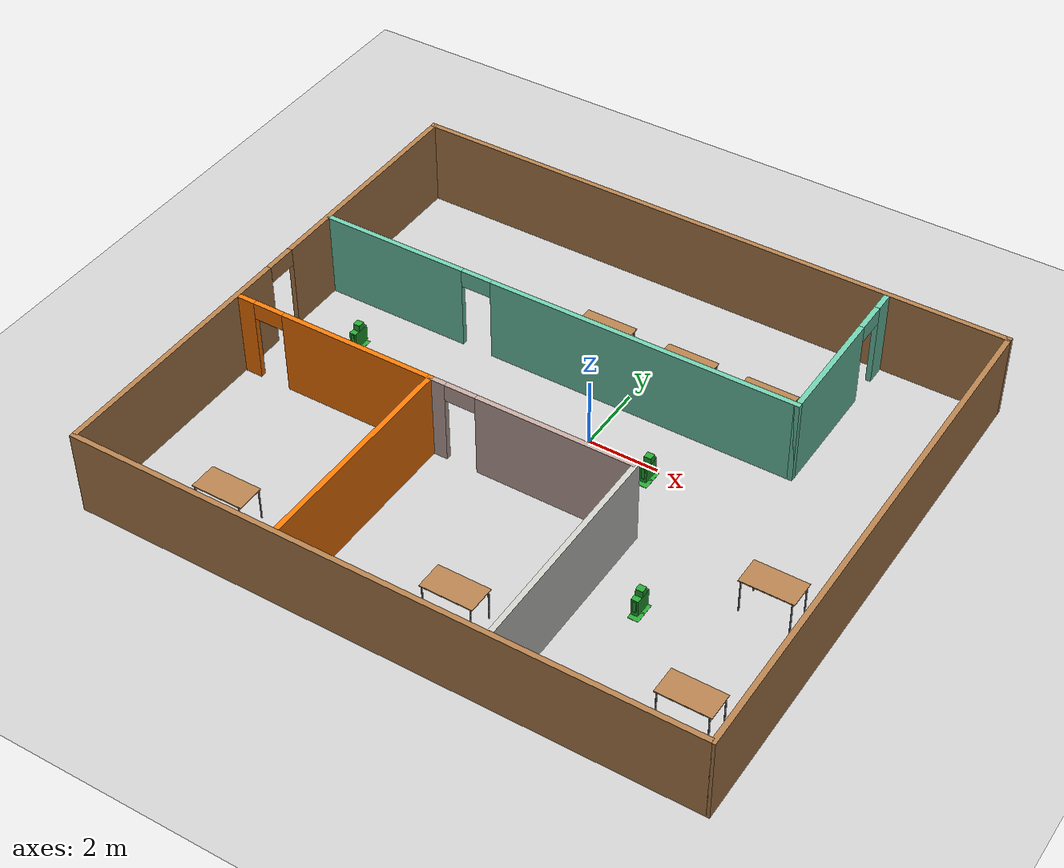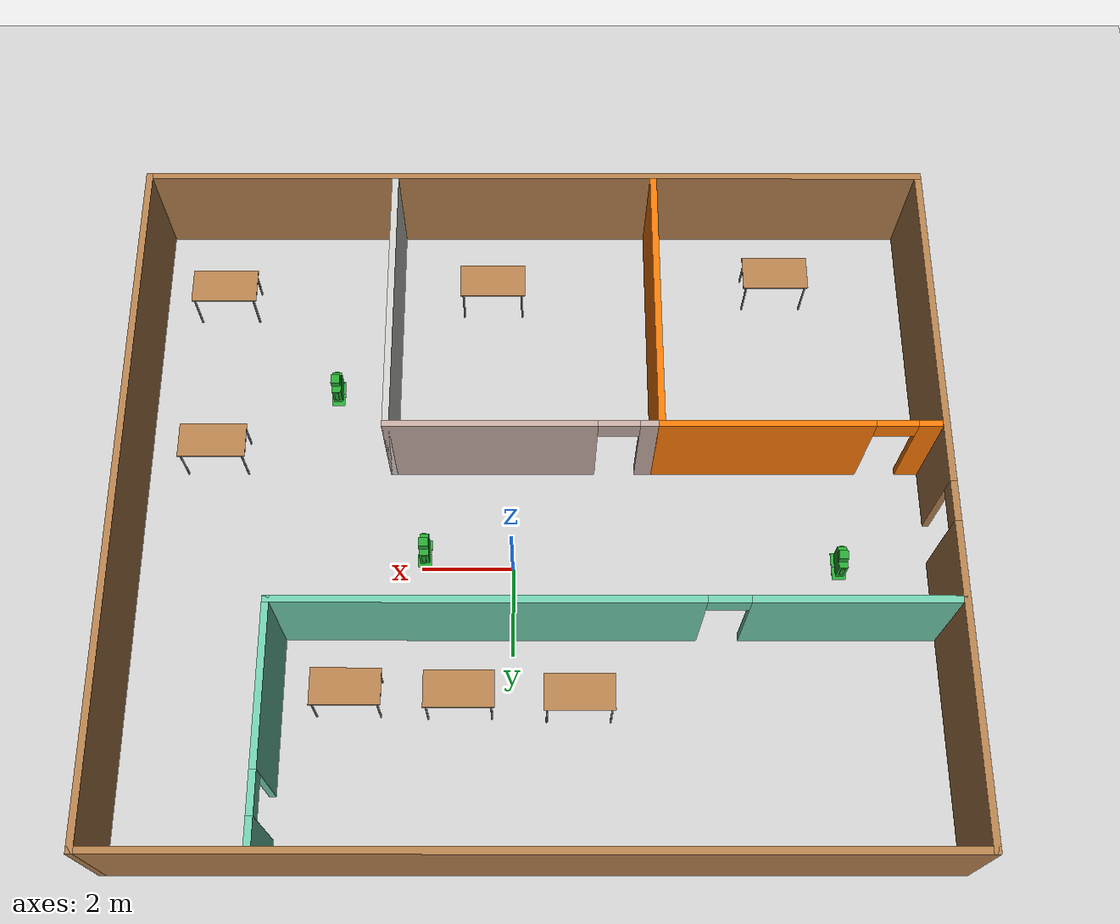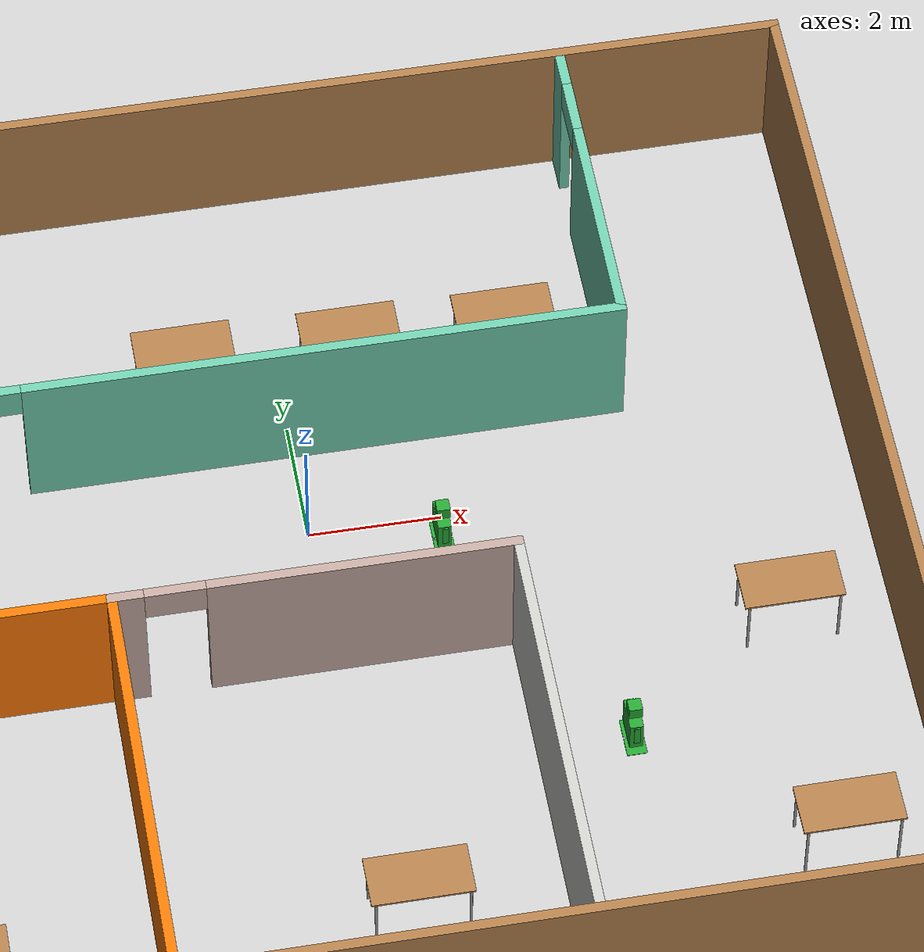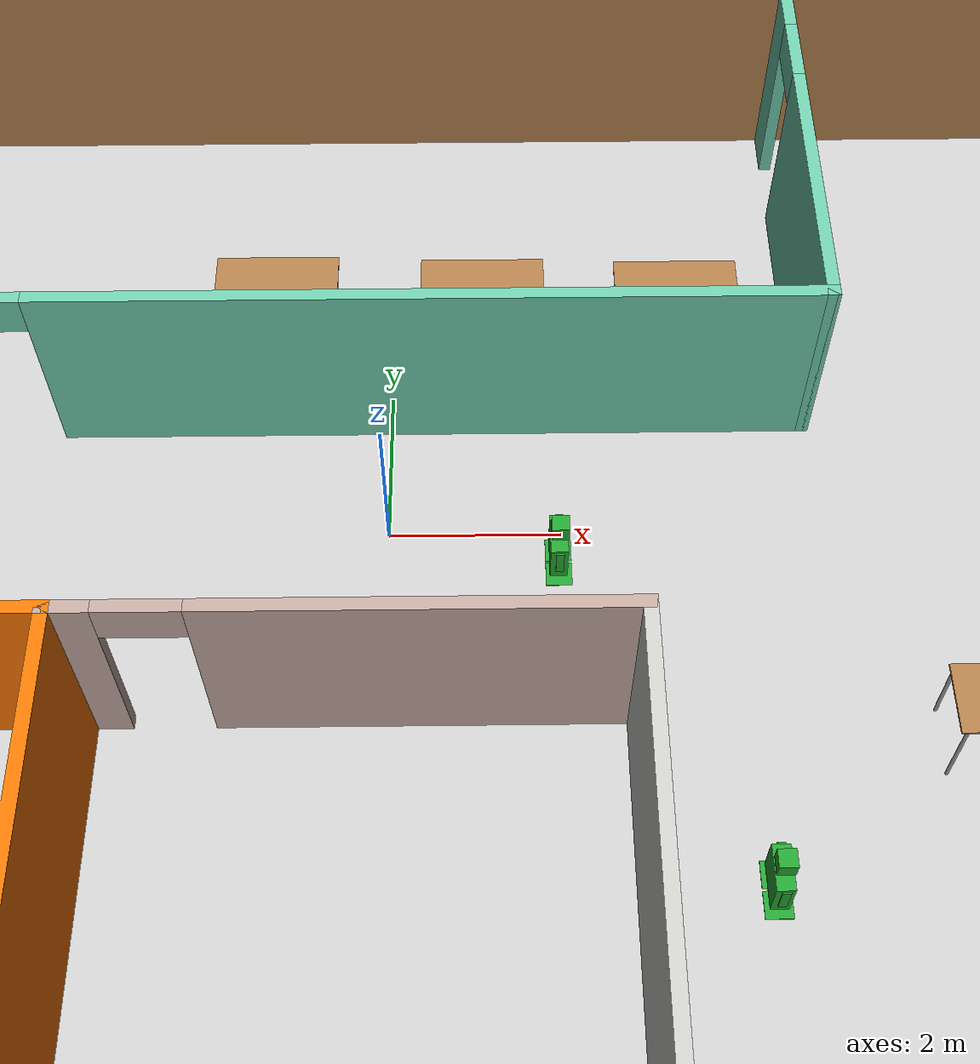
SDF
<sdf version="1.6">
 <world name="default">
  <plugin name="welcome" filename="libwelcome_message.so"/>
  <light name="sun" type="directional">
   <pose>0 0 10 0 -0 0</pose>
   <diffuse>0.8 0.8 0.8 1</diffuse>
   <specular>0.1 0.1 0.1 1</specular>
   <attenuation>
    <range>1000</range>
    <constant>0.9</constant>
    <linear>0.01</linear>
    <quadratic>0.001</quadratic>
   </attenuation>
   <direction>-0.5 0.5 -1</direction>
  </light>
  <model name="ground_plane">
   <static>1</static>
   <link name="link">
    <collision name="collision">
     <geometry><plane><normal>0 0 1</normal><size>100 100</size></plane></geometry>
     <surface><friction><ode><mu>100</mu><mu2>50</mu2></ode></friction></surface>
    </collision>
    <visual name="visual">
     <cast_shadows>0</cast_shadows>
     <geometry><plane><normal>0 0 1</normal><size>100 100</size></plane></geometry>
     <material>
      <script><uri>file://media/materials/scripts/gazebo.material</uri><name>Gazebo/Grey</name></script>
     </material>
    </visual>
   </link>
  </model>
  <gravity>0 0 -9.8</gravity>
  <magnetic_field>6e-06 2.3e-05 -4.2e-05</magnetic_field>
  <atmosphere type="adiabatic"/>
  <physics name="default_physics" default="0" type="ode">
   <max_step_size>0.001</max_step_size>
   <real_time_factor>1</real_time_factor>
   <real_time_update_rate>1000</real_time_update_rate>
  </physics>
  <scene><ambient>0.4 0.4 0.4 1</ambient><background>0.7 0.7 0.7 1</background><shadows>1</shadows></scene>
  <spherical_coordinates>
   <surface_model>EARTH_WGS84</surface_model>
   <latitude_deg>0</latitude_deg>
   <longitude_deg>0</longitude_deg>
   <elevation>0</elevation>
   <heading_deg>0</heading_deg>
  </spherical_coordinates>
  <model name="building_1">
   <pose>-0.446 -1.0545 0 0 -0 0</pose>
   <link name="Wall_42">
    <pose>-8.8 0 0 0 0 -1.5708</pose>
    <visual name="Wall_42_Visual_0">
     <pose>-4.30585 0 1.25 0 -0 0</pose>
     <geometry><box><size>6.83131 0.15 2.5</size></box></geometry>
     <material>
      <script><uri>file://media/materials/scripts/gazebo.material</uri><name>Gazebo/Wood</name></script>
      <ambient>1 1 1 1</ambient>
     </material>
     <meta><layer>0</layer></meta>
    </visual>
    <collision name="Wall_42_Collision_0">
     <geometry><box><size>6.83131 0.15 2.5</size></box></geometry>
     <pose>-4.30585 0 1.25 0 -0 0</pose>
    </collision>
    <visual name="Wall_42_Visual_1">
     <pose>3.86565 0 1.25 0 -0 0</pose>
     <geometry><box><size>7.71169 0.15 2.5</size></box></geometry>
     <material>
      <script><uri>file://media/materials/scripts/gazebo.material</uri><name>Gazebo/Wood</name></script>
      <ambient>1 1 1 1</ambient>
     </material>
     <meta><layer>0</layer></meta>
    </visual>
    <collision name="Wall_42_Collision_1">
     <geometry><box><size>7.71169 0.15 2.5</size></box></geometry>
     <pose>3.86565 0 1.25 0 -0 0</pose>
    </collision>
    <visual name="Wall_42_Visual_2">
     <pose>-0.440192 0 2.25 0 -0 0</pose>
     <geometry><box><size>0.9 0.15 0.5</size></box></geometry>
     <material>
      <script><uri>file://media/materials/scripts/gazebo.material</uri><name>Gazebo/Wood</name></script>
      <ambient>1 1 1 1</ambient>
     </material>
     <meta><layer>0</layer></meta>
    </visual>
    <collision name="Wall_42_Collision_2">
     <geometry><box><size>0.9 0.15 0.5</size></box></geometry>
     <pose>-0.440192 0 2.25 0 -0 0</pose>
    </collision>
   </link>
   <link name="Wall_43">
    <collision name="Wall_43_Collision">
     <geometry><box><size>17.75 0.15 2.5</size></box></geometry>
     <pose>0 0 1.25 0 -0 0</pose>
    </collision>
    <visual name="Wall_43_Visual">
     <pose>0 0 1.25 0 -0 0</pose>
     <geometry><box><size>17.75 0.15 2.5</size></box></geometry>
     <material>
      <script><uri>file://media/materials/scripts/gazebo.material</uri><name>Gazebo/Wood</name></script>
      <ambient>1 1 1 1</ambient>
     </material>
     <meta><layer>0</layer></meta>
    </visual>
    <pose>0 -7.6465 0 0 -0 0</pose>
   </link>
   <link name="Wall_44">
    <collision name="Wall_44_Collision">
     <geometry><box><size>15.443 0.15 2.5</size></box></geometry>
     <pose>0 0 1.25 0 -0 0</pose>
    </collision>
    <visual name="Wall_44_Visual">
     <pose>0 0 1.25 0 -0 0</pose>
     <geometry><box><size>15.443 0.15 2.5</size></box></geometry>
     <material>
      <script><uri>file://media/materials/scripts/gazebo.material</uri><name>Gazebo/Wood</name></script>
      <ambient>1 1 1 1</ambient>
     </material>
     <meta><layer>0</layer></meta>
    </visual>
    <pose>8.8 0 0 0 -0 1.5708</pose>
   </link>
   <link name="Wall_45">
    <collision name="Wall_45_Collision">
     <geometry><box><size>17.75 0.15 2.5</size></box></geometry>
     <pose>0 0 1.25 0 -0 0</pose>
    </collision>
    <visual name="Wall_45_Visual">
     <pose>0 0 1.25 0 -0 0</pose>
     <geometry><box><size>17.75 0.15 2.5</size></box></geometry>
     <material>
      <script><uri>file://media/materials/scripts/gazebo.material</uri><name>Gazebo/Wood</name></script>
      <ambient>1 1 1 1</ambient>
     </material>
     <meta><layer>0</layer></meta>
    </visual>
    <pose>0 7.6465 0 0 -0 3.14159</pose>
   </link>
   <link name="Wall_50">
    <pose>-1.647 2.6095 0 0 -0 0</pose>
    <visual name="Wall_50_Visual_0">
     <pose>-4.97412 0 1.25 0 -0 0</pose>
     <geometry><box><size>4.36782 0.15 2.5</size></box></geometry>
     <material>
      <script><uri>file://media/materials/scripts/gazebo.material</uri><name>Gazebo/Grey</name></script>
      <ambient>0.435294 0.796078 0.67451 1</ambient>
     </material>
     <meta><layer>0</layer></meta>
    </visual>
    <collision name="Wall_50_Collision_0">
     <geometry><box><size>4.36782 0.15 2.5</size></box></geometry>
     <pose>-4.97412 0 1.25 0 -0 0</pose>
    </collision>
    <visual name="Wall_50_Visual_1">
     <pose>2.63391 0 1.25 0 -0 0</pose>
     <geometry><box><size>9.04824 0.15 2.5</size></box></geometry>
     <material>
      <script><uri>file://media/materials/scripts/gazebo.material</uri><name>Gazebo/Grey</name></script>
      <ambient>0.435294 0.796078 0.67451 1</ambient>
     </material>
     <meta><layer>0</layer></meta>
    </visual>
    <collision name="Wall_50_Collision_1">
     <geometry><box><size>9.04824 0.15 2.5</size></box></geometry>
     <pose>2.63391 0 1.25 0 -0 0</pose>
    </collision>
    <visual name="Wall_50_Visual_2">
     <pose>-2.34021 0 2.25 0 -0 0</pose>
     <geometry><box><size>0.9 0.15 0.5</size></box></geometry>
     <material>
      <script><uri>file://media/materials/scripts/gazebo.material</uri><name>Gazebo/Grey</name></script>
      <ambient>0.435294 0.796078 0.67451 1</ambient>
     </material>
     <meta><layer>0</layer></meta>
    </visual>
    <collision name="Wall_50_Collision_2">
     <geometry><box><size>0.9 0.15 0.5</size></box></geometry>
     <pose>-2.34021 0 2.25 0 -0 0</pose>
    </collision>
   </link>
   <link name="Wall_51">
    <pose>5.436 5.052 0 0 -0 1.5708</pose>
    <visual name="Wall_51_Visual_0">
     <pose>-0.73569 0 1.25 0 -0 0</pose>
     <geometry><box><size>3.56362 0.15 2.5</size></box></geometry>
     <material>
      <script><uri>file://media/materials/scripts/gazebo.material</uri><name>Gazebo/Grey</name></script>
      <ambient>0.435294 0.796078 0.67451 1</ambient>
     </material>
     <meta><layer>0</layer></meta>
    </visual>
    <collision name="Wall_51_Collision_0">
     <geometry><box><size>3.56362 0.15 2.5</size></box></geometry>
     <pose>-0.73569 0 1.25 0 -0 0</pose>
    </collision>
    <visual name="Wall_51_Visual_1">
     <pose>2.23181 0 1.25 0 -0 0</pose>
     <geometry><box><size>0.57138 0.15 2.5</size></box></geometry>
     <material>
      <script><uri>file://media/materials/scripts/gazebo.material</uri><name>Gazebo/Grey</name></script>
      <ambient>0.435294 0.796078 0.67451 1</ambient>
     </material>
     <meta><layer>0</layer></meta>
    </visual>
    <collision name="Wall_51_Collision_1">
     <geometry><box><size>0.57138 0.15 2.5</size></box></geometry>
     <pose>2.23181 0 1.25 0 -0 0</pose>
    </collision>
    <visual name="Wall_51_Visual_2">
     <pose>1.49612 0 2.25 0 -0 0</pose>
     <geometry><box><size>0.9 0.15 0.5</size></box></geometry>
     <material>
      <script><uri>file://media/materials/scripts/gazebo.material</uri><name>Gazebo/Grey</name></script>
      <ambient>0.435294 0.796078 0.67451 1</ambient>
     </material>
     <meta><layer>0</layer></meta>
    </visual>
    <collision name="Wall_51_Collision_2">
     <geometry><box><size>0.9 0.15 0.5</size></box></geometry>
     <pose>1.49612 0 2.25 0 -0 0</pose>
    </collision>
   </link>
   <link name="Wall_54">
    <pose>-5.695 -1.3425 0 0 -0 0</pose>
    <visual name="Wall_54_Visual_0">
     <pose>-2.77183 0 1.25 0 -0 0</pose>
     <geometry><box><size>0.512338 0.15 2.5</size></box></geometry>
     <material>
      <script><uri>file://media/materials/scripts/gazebo.material</uri><name>Gazebo/Grey</name></script>
      <ambient>0.996078 0.47451 0.0196078 1</ambient>
     </material>
     <meta><layer>0</layer></meta>
    </visual>
    <collision name="Wall_54_Collision_0">
     <geometry><box><size>0.512338 0.15 2.5</size></box></geometry>
     <pose>-2.77183 0 1.25 0 -0 0</pose>
    </collision>
    <visual name="Wall_54_Visual_1">
     <pose>0.706169 0 1.25 0 -0 0</pose>
     <geometry><box><size>4.64366 0.15 2.5</size></box></geometry>
     <material>
      <script><uri>file://media/materials/scripts/gazebo.material</uri><name>Gazebo/Grey</name></script>
      <ambient>0.996078 0.47451 0.0196078 1</ambient>
     </material>
     <meta><layer>0</layer></meta>
    </visual>
    <collision name="Wall_54_Collision_1">
     <geometry><box><size>4.64366 0.15 2.5</size></box></geometry>
     <pose>0.706169 0 1.25 0 -0 0</pose>
    </collision>
    <visual name="Wall_54_Visual_2">
     <pose>-2.06566 0 2.25 0 -0 0</pose>
     <geometry><box><size>0.9 0.15 0.5</size></box></geometry>
     <material>
      <script><uri>file://media/materials/scripts/gazebo.material</uri><name>Gazebo/Grey</name></script>
      <ambient>0.996078 0.47451 0.0196078 1</ambient>
     </material>
     <meta><layer>0</layer></meta>
    </visual>
    <collision name="Wall_54_Collision_2">
     <geometry><box><size>0.9 0.15 0.5</size></box></geometry>
     <pose>-2.06566 0 2.25 0 -0 0</pose>
    </collision>
   </link>
   <link name="Wall_55">
    <collision name="Wall_55_Collision">
     <geometry><box><size>6.303 0.15 2.5</size></box></geometry>
     <pose>0 0 1.25 0 -0 0</pose>
    </collision>
    <visual name="Wall_55_Visual">
     <pose>0 0 1.25 0 -0 0</pose>
     <geometry><box><size>6.303 0.15 2.5</size></box></geometry>
     <material>
      <script><uri>file://media/materials/scripts/gazebo.material</uri><name>Gazebo/Grey</name></script>
      <ambient>0.996078 0.47451 0.0196078 1</ambient>
     </material>
     <meta><layer>0</layer></meta>
    </visual>
    <pose>-2.742 -4.419 0 0 0 -1.5708</pose>
   </link>
   <link name="Wall_58">
    <pose>0.211 -1.3425 0 0 -0 0</pose>
    <visual name="Wall_58_Visual_0">
     <pose>-2.75873 0 1.25 0 -0 0</pose>
     <geometry><box><size>0.538542 0.15 2.5</size></box></geometry>
     <material>
      <script><uri>file://media/materials/scripts/gazebo.material</uri><name>Gazebo/Grey</name></script>
      <ambient>0.760784 0.662745 0.627451 1</ambient>
     </material>
     <meta><layer>0</layer></meta>
    </visual>
    <collision name="Wall_58_Collision_0">
     <geometry><box><size>0.538542 0.15 2.5</size></box></geometry>
     <pose>-2.75873 0 1.25 0 -0 0</pose>
    </collision>
    <visual name="Wall_58_Visual_1">
     <pose>0.719271 0 1.25 0 -0 0</pose>
     <geometry><box><size>4.61746 0.15 2.5</size></box></geometry>
     <material>
      <script><uri>file://media/materials/scripts/gazebo.material</uri><name>Gazebo/Grey</name></script>
      <ambient>0.760784 0.662745 0.627451 1</ambient>
     </material>
     <meta><layer>0</layer></meta>
    </visual>
    <collision name="Wall_58_Collision_1">
     <geometry><box><size>4.61746 0.15 2.5</size></box></geometry>
     <pose>0.719271 0 1.25 0 -0 0</pose>
    </collision>
    <visual name="Wall_58_Visual_2">
     <pose>-2.03946 0 2.25 0 -0 0</pose>
     <geometry><box><size>0.9 0.15 0.5</size></box></geometry>
     <material>
      <script><uri>file://media/materials/scripts/gazebo.material</uri><name>Gazebo/Grey</name></script>
      <ambient>0.760784 0.662745 0.627451 1</ambient>
     </material>
     <meta><layer>0</layer></meta>
    </visual>
    <collision name="Wall_58_Collision_2">
     <geometry><box><size>0.9 0.15 0.5</size></box></geometry>
     <pose>-2.03946 0 2.25 0 -0 0</pose>
    </collision>
   </link>
   <link name="Wall_59">
    <collision name="Wall_59_Collision">
     <geometry><box><size>6.303 0.15 2.5</size></box></geometry>
     <pose>0 0 1.25 0 -0 0</pose>
    </collision>
    <visual name="Wall_59_Visual">
     <pose>0 0 1.25 0 -0 0</pose>
     <geometry><box><size>6.303 0.15 2.5</size></box></geometry>
     <material>
      <script><uri>file://media/materials/scripts/gazebo.material</uri><name>Gazebo/CeilingTiled</name></script>
      <ambient>1 1 1 1</ambient>
     </material>
     <meta><layer>0</layer></meta>
    </visual>
    <pose>3.164 -4.419 0 0 0 -1.5708</pose>
   </link>
   <static>1</static>
  </model>
  <model name="table">
   <static>1</static>
   <link name="link">
    <collision name="surface">
     <pose>0 0 1 0 -0 0</pose>
     <geometry><box><size>1.5 0.8 0.03</size></box></geometry>
     <surface><friction><ode><mu>0.6</mu><mu2>0.6</mu2></ode></friction></surface>
    </collision>
    <visual name="visual1">
     <pose>0 0 1 0 -0 0</pose>
     <geometry><box><size>1.5 0.8 0.03</size></box></geometry>
     <material>
      <script><uri>file://media/materials/scripts/gazebo.material</uri><name>Gazebo/Wood</name></script>
     </material>
    </visual>
    <collision name="front_left_leg">
     <pose>0.68 0.38 0.5 0 -0 0</pose>
     <geometry><cylinder><radius>0.02</radius><length>1</length></cylinder></geometry>
    </collision>
    <visual name="front_left_leg">
     <pose>0.68 0.38 0.5 0 -0 0</pose>
     <geometry><cylinder><radius>0.02</radius><length>1</length></cylinder></geometry>
     <material>
      <script><uri>file://media/materials/scripts/gazebo.material</uri><name>Gazebo/Grey</name></script>
     </material>
    </visual>
    <collision name="front_right_leg">
     <pose>0.68 -0.38 0.5 0 -0 0</pose>
     <geometry><cylinder><radius>0.02</radius><length>1</length></cylinder></geometry>
    </collision>
    <visual name="front_right_leg">
     <pose>0.68 -0.38 0.5 0 -0 0</pose>
     <geometry><cylinder><radius>0.02</radius><length>1</length></cylinder></geometry>
     <material>
      <script><uri>file://media/materials/scripts/gazebo.material</uri><name>Gazebo/Grey</name></script>
     </material>
    </visual>
    <collision name="back_right_leg">
     <pose>-0.68 -0.38 0.5 0 -0 0</pose>
     <geometry><cylinder><radius>0.02</radius><length>1</length></cylinder></geometry>
    </collision>
    <visual name="back_right_leg">
     <pose>-0.68 -0.38 0.5 0 -0 0</pose>
     <geometry><cylinder><radius>0.02</radius><length>1</length></cylinder></geometry>
     <material>
      <script><uri>file://media/materials/scripts/gazebo.material</uri><name>Gazebo/Grey</name></script>
     </material>
    </visual>
    <collision name="back_left_leg">
     <pose>-0.68 0.38 0.5 0 -0 0</pose>
     <geometry><cylinder><radius>0.02</radius><length>1</length></cylinder></geometry>
    </collision>
    <visual name="back_left_leg">
     <pose>-0.68 0.38 0.5 0 -0 0</pose>
     <geometry><cylinder><radius>0.02</radius><length>1</length></cylinder></geometry>
     <material>
      <script><uri>file://media/materials/scripts/gazebo.material</uri><name>Gazebo/Grey</name></script>
     </material>
    </visual>
   </link>
   <pose>3.47581 2.95191 0 0 -0 0</pose>
  </model>
  <model name="table_0">
   <static>1</static>
   <link name="link">
    <collision name="surface">
     <pose>0 0 1 0 -0 0</pose>
     <geometry><box><size>1.5 0.8 0.03</size></box></geometry>
     <surface><friction><ode><mu>0.6</mu><mu2>0.6</mu2></ode></friction></surface>
    </collision>
    <visual name="visual1">
     <pose>0 0 1 0 -0 0</pose>
     <geometry><box><size>1.5 0.8 0.03</size></box></geometry>
     <material>
      <script><uri>file://media/materials/scripts/gazebo.material</uri><name>Gazebo/Wood</name></script>
     </material>
    </visual>
    <collision name="front_left_leg">
     <pose>0.68 0.38 0.5 0 -0 0</pose>
     <geometry><cylinder><radius>0.02</radius><length>1</length></cylinder></geometry>
    </collision>
    <visual name="front_left_leg">
     <pose>0.68 0.38 0.5 0 -0 0</pose>
     <geometry><cylinder><radius>0.02</radius><length>1</length></cylinder></geometry>
     <material>
      <script><uri>file://media/materials/scripts/gazebo.material</uri><name>Gazebo/Grey</name></script>
     </material>
    </visual>
    <collision name="front_right_leg">
     <pose>0.68 -0.38 0.5 0 -0 0</pose>
     <geometry><cylinder><radius>0.02</radius><length>1</length></cylinder></geometry>
    </collision>
    <visual name="front_right_leg">
     <pose>0.68 -0.38 0.5 0 -0 0</pose>
     <geometry><cylinder><radius>0.02</radius><length>1</length></cylinder></geometry>
     <material>
      <script><uri>file://media/materials/scripts/gazebo.material</uri><name>Gazebo/Grey</name></script>
     </material>
    </visual>
    <collision name="back_right_leg">
     <pose>-0.68 -0.38 0.5 0 -0 0</pose>
     <geometry><cylinder><radius>0.02</radius><length>1</length></cylinder></geometry>
    </collision>
    <visual name="back_right_leg">
     <pose>-0.68 -0.38 0.5 0 -0 0</pose>
     <geometry><cylinder><radius>0.02</radius><length>1</length></cylinder></geometry>
     <material>
      <script><uri>file://media/materials/scripts/gazebo.material</uri><name>Gazebo/Grey</name></script>
     </material>
    </visual>
    <collision name="back_left_leg">
     <pose>-0.68 0.38 0.5 0 -0 0</pose>
     <geometry><cylinder><radius>0.02</radius><length>1</length></cylinder></geometry>
    </collision>
    <visual name="back_left_leg">
     <pose>-0.68 0.38 0.5 0 -0 0</pose>
     <geometry><cylinder><radius>0.02</radius><length>1</length></cylinder></geometry>
     <material>
      <script><uri>file://media/materials/scripts/gazebo.material</uri><name>Gazebo/Grey</name></script>
     </material>
    </visual>
   </link>
   <pose>1.10733 3.00135 0 0 -0 0</pose>
  </model>
  <model name="table_1">
   <static>1</static>
   <link name="link">
    <collision name="surface">
     <pose>0 0 1 0 -0 0</pose>
     <geometry><box><size>1.5 0.8 0.03</size></box></geometry>
     <surface><friction><ode><mu>0.6</mu><mu2>0.6</mu2></ode></friction></surface>
    </collision>
    <visual name="visual1">
     <pose>0 0 1 0 -0 0</pose>
     <geometry><box><size>1.5 0.8 0.03</size></box></geometry>
     <material>
      <script><uri>file://media/materials/scripts/gazebo.material</uri><name>Gazebo/Wood</name></script>
     </material>
    </visual>
    <collision name="front_left_leg">
     <pose>0.68 0.38 0.5 0 -0 0</pose>
     <geometry><cylinder><radius>0.02</radius><length>1</length></cylinder></geometry>
    </collision>
    <visual name="front_left_leg">
     <pose>0.68 0.38 0.5 0 -0 0</pose>
     <geometry><cylinder><radius>0.02</radius><length>1</length></cylinder></geometry>
     <material>
      <script><uri>file://media/materials/scripts/gazebo.material</uri><name>Gazebo/Grey</name></script>
     </material>
    </visual>
    <collision name="front_right_leg">
     <pose>0.68 -0.38 0.5 0 -0 0</pose>
     <geometry><cylinder><radius>0.02</radius><length>1</length></cylinder></geometry>
    </collision>
    <visual name="front_right_leg">
     <pose>0.68 -0.38 0.5 0 -0 0</pose>
     <geometry><cylinder><radius>0.02</radius><length>1</length></cylinder></geometry>
     <material>
      <script><uri>file://media/materials/scripts/gazebo.material</uri><name>Gazebo/Grey</name></script>
     </material>
    </visual>
    <collision name="back_right_leg">
     <pose>-0.68 -0.38 0.5 0 -0 0</pose>
     <geometry><cylinder><radius>0.02</radius><length>1</length></cylinder></geometry>
    </collision>
    <visual name="back_right_leg">
     <pose>-0.68 -0.38 0.5 0 -0 0</pose>
     <geometry><cylinder><radius>0.02</radius><length>1</length></cylinder></geometry>
     <material>
      <script><uri>file://media/materials/scripts/gazebo.material</uri><name>Gazebo/Grey</name></script>
     </material>
    </visual>
    <collision name="back_left_leg">
     <pose>-0.68 0.38 0.5 0 -0 0</pose>
     <geometry><cylinder><radius>0.02</radius><length>1</length></cylinder></geometry>
    </collision>
    <visual name="back_left_leg">
     <pose>-0.68 0.38 0.5 0 -0 0</pose>
     <geometry><cylinder><radius>0.02</radius><length>1</length></cylinder></geometry>
     <material>
      <script><uri>file://media/materials/scripts/gazebo.material</uri><name>Gazebo/Grey</name></script>
     </material>
    </visual>
   </link>
   <pose>-1.40994 3.06696 0 0 -0 0</pose>
  </model>
  <model name="table_2">
   <static>1</static>
   <link name="link">
    <collision name="surface">
     <pose>0 0 1 0 -0 0</pose>
     <geometry><box><size>1.5 0.8 0.03</size></box></geometry>
     <surface><friction><ode><mu>0.6</mu><mu2>0.6</mu2></ode></friction></surface>
    </collision>
    <visual name="visual1">
     <pose>0 0 1 0 -0 0</pose>
     <geometry><box><size>1.5 0.8 0.03</size></box></geometry>
     <material>
      <script><uri>file://media/materials/scripts/gazebo.material</uri><name>Gazebo/Wood</name></script>
     </material>
    </visual>
    <collision name="front_left_leg">
     <pose>0.68 0.38 0.5 0 -0 0</pose>
     <geometry><cylinder><radius>0.02</radius><length>1</length></cylinder></geometry>
    </collision>
    <visual name="front_left_leg">
     <pose>0.68 0.38 0.5 0 -0 0</pose>
     <geometry><cylinder><radius>0.02</radius><length>1</length></cylinder></geometry>
     <material>
      <script><uri>file://media/materials/scripts/gazebo.material</uri><name>Gazebo/Grey</name></script>
     </material>
    </visual>
    <collision name="front_right_leg">
     <pose>0.68 -0.38 0.5 0 -0 0</pose>
     <geometry><cylinder><radius>0.02</radius><length>1</length></cylinder></geometry>
    </collision>
    <visual name="front_right_leg">
     <pose>0.68 -0.38 0.5 0 -0 0</pose>
     <geometry><cylinder><radius>0.02</radius><length>1</length></cylinder></geometry>
     <material>
      <script><uri>file://media/materials/scripts/gazebo.material</uri><name>Gazebo/Grey</name></script>
     </material>
    </visual>
    <collision name="back_right_leg">
     <pose>-0.68 -0.38 0.5 0 -0 0</pose>
     <geometry><cylinder><radius>0.02</radius><length>1</length></cylinder></geometry>
    </collision>
    <visual name="back_right_leg">
     <pose>-0.68 -0.38 0.5 0 -0 0</pose>
     <geometry><cylinder><radius>0.02</radius><length>1</length></cylinder></geometry>
     <material>
      <script><uri>file://media/materials/scripts/gazebo.material</uri><name>Gazebo/Grey</name></script>
     </material>
    </visual>
    <collision name="back_left_leg">
     <pose>-0.68 0.38 0.5 0 -0 0</pose>
     <geometry><cylinder><radius>0.02</radius><length>1</length></cylinder></geometry>
    </collision>
    <visual name="back_left_leg">
     <pose>-0.68 0.38 0.5 0 -0 0</pose>
     <geometry><cylinder><radius>0.02</radius><length>1</length></cylinder></geometry>
     <material>
      <script><uri>file://media/materials/scripts/gazebo.material</uri><name>Gazebo/Grey</name></script>
     </material>
    </visual>
   </link>
   <pose>0.503693 -6.82744 0 0 -0 0</pose>
  </model>
  <model name="table_3">
   <static>1</static>
   <link name="link">
    <collision name="surface">
     <pose>0 0 1 0 -0 0</pose>
     <geometry><box><size>1.5 0.8 0.03</size></box></geometry>
     <surface><friction><ode><mu>0.6</mu><mu2>0.6</mu2></ode></friction></surface>
    </collision>
    <visual name="visual1">
     <pose>0 0 1 0 -0 0</pose>
     <geometry><box><size>1.5 0.8 0.03</size></box></geometry>
     <material>
      <script><uri>file://media/materials/scripts/gazebo.material</uri><name>Gazebo/Wood</name></script>
     </material>
    </visual>
    <collision name="front_left_leg">
     <pose>0.68 0.38 0.5 0 -0 0</pose>
     <geometry><cylinder><radius>0.02</radius><length>1</length></cylinder></geometry>
    </collision>
    <visual name="front_left_leg">
     <pose>0.68 0.38 0.5 0 -0 0</pose>
     <geometry><cylinder><radius>0.02</radius><length>1</length></cylinder></geometry>
     <material>
      <script><uri>file://media/materials/scripts/gazebo.material</uri><name>Gazebo/Grey</name></script>
     </material>
    </visual>
    <collision name="front_right_leg">
     <pose>0.68 -0.38 0.5 0 -0 0</pose>
     <geometry><cylinder><radius>0.02</radius><length>1</length></cylinder></geometry>
    </collision>
    <visual name="front_right_leg">
     <pose>0.68 -0.38 0.5 0 -0 0</pose>
     <geometry><cylinder><radius>0.02</radius><length>1</length></cylinder></geometry>
     <material>
      <script><uri>file://media/materials/scripts/gazebo.material</uri><name>Gazebo/Grey</name></script>
     </material>
    </visual>
    <collision name="back_right_leg">
     <pose>-0.68 -0.38 0.5 0 -0 0</pose>
     <geometry><cylinder><radius>0.02</radius><length>1</length></cylinder></geometry>
    </collision>
    <visual name="back_right_leg">
     <pose>-0.68 -0.38 0.5 0 -0 0</pose>
     <geometry><cylinder><radius>0.02</radius><length>1</length></cylinder></geometry>
     <material>
      <script><uri>file://media/materials/scripts/gazebo.material</uri><name>Gazebo/Grey</name></script>
     </material>
    </visual>
    <collision name="back_left_leg">
     <pose>-0.68 0.38 0.5 0 -0 0</pose>
     <geometry><cylinder><radius>0.02</radius><length>1</length></cylinder></geometry>
    </collision>
    <visual name="back_left_leg">
     <pose>-0.68 0.38 0.5 0 -0 0</pose>
     <geometry><cylinder><radius>0.02</radius><length>1</length></cylinder></geometry>
     <material>
      <script><uri>file://media/materials/scripts/gazebo.material</uri><name>Gazebo/Grey</name></script>
     </material>
    </visual>
   </link>
   <pose>-6.08995 -7.03681 0 0 -0 0</pose>
  </model>
  <model name="table_4">
   <static>1</static>
   <link name="link">
    <collision name="surface">
     <pose>0 0 1 0 -0 0</pose>
     <geometry><box><size>1.5 0.8 0.03</size></box></geometry>
     <surface><friction><ode><mu>0.6</mu><mu2>0.6</mu2></ode></friction></surface>
    </collision>
    <visual name="visual1">
     <pose>0 0 1 0 -0 0</pose>
     <geometry><box><size>1.5 0.8 0.03</size></box></geometry>
     <material>
      <script><uri>file://media/materials/scripts/gazebo.material</uri><name>Gazebo/Wood</name></script>
     </material>
    </visual>
    <collision name="front_left_leg">
     <pose>0.68 0.38 0.5 0 -0 0</pose>
     <geometry><cylinder><radius>0.02</radius><length>1</length></cylinder></geometry>
    </collision>
    <visual name="front_left_leg">
     <pose>0.68 0.38 0.5 0 -0 0</pose>
     <geometry><cylinder><radius>0.02</radius><length>1</length></cylinder></geometry>
     <material>
      <script><uri>file://media/materials/scripts/gazebo.material</uri><name>Gazebo/Grey</name></script>
     </material>
    </visual>
    <collision name="front_right_leg">
     <pose>0.68 -0.38 0.5 0 -0 0</pose>
     <geometry><cylinder><radius>0.02</radius><length>1</length></cylinder></geometry>
    </collision>
    <visual name="front_right_leg">
     <pose>0.68 -0.38 0.5 0 -0 0</pose>
     <geometry><cylinder><radius>0.02</radius><length>1</length></cylinder></geometry>
     <material>
      <script><uri>file://media/materials/scripts/gazebo.material</uri><name>Gazebo/Grey</name></script>
     </material>
    </visual>
    <collision name="back_right_leg">
     <pose>-0.68 -0.38 0.5 0 -0 0</pose>
     <geometry><cylinder><radius>0.02</radius><length>1</length></cylinder></geometry>
    </collision>
    <visual name="back_right_leg">
     <pose>-0.68 -0.38 0.5 0 -0 0</pose>
     <geometry><cylinder><radius>0.02</radius><length>1</length></cylinder></geometry>
     <material>
      <script><uri>file://media/materials/scripts/gazebo.material</uri><name>Gazebo/Grey</name></script>
     </material>
    </visual>
    <collision name="back_left_leg">
     <pose>-0.68 0.38 0.5 0 -0 0</pose>
     <geometry><cylinder><radius>0.02</radius><length>1</length></cylinder></geometry>
    </collision>
    <visual name="back_left_leg">
     <pose>-0.68 0.38 0.5 0 -0 0</pose>
     <geometry><cylinder><radius>0.02</radius><length>1</length></cylinder></geometry>
     <material>
      <script><uri>file://media/materials/scripts/gazebo.material</uri><name>Gazebo/Grey</name></script>
     </material>
    </visual>
   </link>
   <pose>6.74449 -6.68244 0 0 -0 0</pose>
  </model>
  <model name="table_5">
   <static>1</static>
   <link name="link">
    <collision name="surface">
     <pose>0 0 1 0 -0 0</pose>
     <geometry><box><size>1.5 0.8 0.03</size></box></geometry>
     <surface><friction><ode><mu>0.6</mu><mu2>0.6</mu2></ode></friction></surface>
    </collision>
    <visual name="visual1">
     <pose>0 0 1 0 -0 0</pose>
     <geometry><box><size>1.5 0.8 0.03</size></box></geometry>
     <material>
      <script><uri>file://media/materials/scripts/gazebo.material</uri><name>Gazebo/Wood</name></script>
     </material>
    </visual>
    <collision name="front_left_leg">
     <pose>0.68 0.38 0.5 0 -0 0</pose>
     <geometry><cylinder><radius>0.02</radius><length>1</length></cylinder></geometry>
    </collision>
    <visual name="front_left_leg">
     <pose>0.68 0.38 0.5 0 -0 0</pose>
     <geometry><cylinder><radius>0.02</radius><length>1</length></cylinder></geometry>
     <material>
      <script><uri>file://media/materials/scripts/gazebo.material</uri><name>Gazebo/Grey</name></script>
     </material>
    </visual>
    <collision name="front_right_leg">
     <pose>0.68 -0.38 0.5 0 -0 0</pose>
     <geometry><cylinder><radius>0.02</radius><length>1</length></cylinder></geometry>
    </collision>
    <visual name="front_right_leg">
     <pose>0.68 -0.38 0.5 0 -0 0</pose>
     <geometry><cylinder><radius>0.02</radius><length>1</length></cylinder></geometry>
     <material>
      <script><uri>file://media/materials/scripts/gazebo.material</uri><name>Gazebo/Grey</name></script>
     </material>
    </visual>
    <collision name="back_right_leg">
     <pose>-0.68 -0.38 0.5 0 -0 0</pose>
     <geometry><cylinder><radius>0.02</radius><length>1</length></cylinder></geometry>
    </collision>
    <visual name="back_right_leg">
     <pose>-0.68 -0.38 0.5 0 -0 0</pose>
     <geometry><cylinder><radius>0.02</radius><length>1</length></cylinder></geometry>
     <material>
      <script><uri>file://media/materials/scripts/gazebo.material</uri><name>Gazebo/Grey</name></script>
     </material>
    </visual>
    <collision name="back_left_leg">
     <pose>-0.68 0.38 0.5 0 -0 0</pose>
     <geometry><cylinder><radius>0.02</radius><length>1</length></cylinder></geometry>
    </collision>
    <visual name="back_left_leg">
     <pose>-0.68 0.38 0.5 0 -0 0</pose>
     <geometry><cylinder><radius>0.02</radius><length>1</length></cylinder></geometry>
     <material>
      <script><uri>file://media/materials/scripts/gazebo.material</uri><name>Gazebo/Grey</name></script>
     </material>
    </visual>
   </link>
   <pose>6.71633 -2.72133 0 0 -0 0</pose>
  </model>
  <model name="robot">
   <link name="foot_1">
    <pose>-0.002177 -0.002528 -0.025294 0 -0 0</pose>
    <inertial>
     <mass>1</mass>
     <inertia>
      <ixx>0.166667</ixx>
      <ixy>0</ixy>
      <ixz>0</ixz>
      <iyy>0.166667</iyy>
      <iyz>0</iyz>
      <izz>0.166667</izz>
     </inertia>
    </inertial>
    <visual name="visual">
     <geometry><box><size>0.3 0.3 0.01</size></box></geometry>
     <material>
      <lighting>1</lighting>
      <script><uri>file://media/materials/scripts/gazebo.material</uri><name>Gazebo/Green</name></script>
     </material>
    </visual>
    <collision name="collision">
     <geometry><box><size>0.3 0.3 0.01</size></box></geometry>
     <surface>
      <friction>
       <ode><mu>1</mu><mu2>1</mu2><fdir1>0 0 0</fdir1><slip1>0</slip1><slip2>0</slip2></ode>
       <torsional>
        <coefficient>1</coefficient>
        <patch_radius>0</patch_radius>
        <surface_radius>0</surface_radius>
        <use_patch_radius>1</use_patch_radius>
        <ode><slip>0</slip></ode>
       </torsional>
      </friction>
      <bounce><restitution_coefficient>0</restitution_coefficient><threshold>1e+06</threshold></bounce>
      <contact>
       <collide_without_contact>0</collide_without_contact>
       <collide_without_contact_bitmask>1</collide_without_contact_bitmask>
       <collide_bitmask>1</collide_bitmask>
       <ode>
        <soft_cfm>0</soft_cfm>
        <soft_erp>0.2</soft_erp>
        <kp>1e+13</kp>
        <kd>1</kd>
        <max_vel>0.01</max_vel>
        <min_depth>0</min_depth>
       </ode>
       <bullet>
        <split_impulse>1</split_impulse>
        <split_impulse_penetration_threshold>-0.01</split_impulse_penetration_threshold>
        <soft_cfm>0</soft_cfm>
        <soft_erp>0.2</soft_erp>
        <kp>1e+13</kp>
        <kd>1</kd>
       </bullet>
      </contact>
     </surface>
    </collision>
   </link>
   <link name="arm_1">
    <pose>-0.003122 -0.091998 0.37 -3e-06 -0 -2e-05</pose>
    <inertial>
     <mass>1</mass>
     <inertia>
      <ixx>0.166667</ixx>
      <ixy>0</ixy>
      <ixz>0</ixz>
      <iyy>0.166667</iyy>
      <iyz>0</iyz>
      <izz>0.166667</izz>
     </inertia>
    </inertial>
    <visual name="visual">
     <geometry><box><size>0.09 0.02 0.35</size></box></geometry>
     <material>
      <lighting>1</lighting>
      <script><uri>file://media/materials/scripts/gazebo.material</uri><name>Gazebo/Green</name></script>
     </material>
    </visual>
    <collision name="collision">
     <geometry><box><size>0.09 0.02 0.35</size></box></geometry>
     <surface>
      <friction>
       <ode><mu>1</mu><mu2>1</mu2><fdir1>0 0 0</fdir1><slip1>0</slip1><slip2>0</slip2></ode>
       <torsional>
        <coefficient>1</coefficient>
        <patch_radius>0</patch_radius>
        <surface_radius>0</surface_radius>
        <use_patch_radius>1</use_patch_radius>
        <ode><slip>0</slip></ode>
       </torsional>
      </friction>
      <bounce><restitution_coefficient>0</restitution_coefficient><threshold>1e+06</threshold></bounce>
      <contact>
       <collide_without_contact>0</collide_without_contact>
       <collide_without_contact_bitmask>1</collide_without_contact_bitmask>
       <collide_bitmask>1</collide_bitmask>
       <ode>
        <soft_cfm>0</soft_cfm>
        <soft_erp>0.2</soft_erp>
        <kp>1e+13</kp>
        <kd>1</kd>
        <max_vel>0.01</max_vel>
        <min_depth>0</min_depth>
       </ode>
       <bullet>
        <split_impulse>1</split_impulse>
        <split_impulse_penetration_threshold>-0.01</split_impulse_penetration_threshold>
        <soft_cfm>0</soft_cfm>
        <soft_erp>0.2</soft_erp>
        <kp>1e+13</kp>
        <kd>1</kd>
       </bullet>
      </contact>
     </surface>
    </collision>
   </link>
   <link name="arm_2">
    <pose>-0.003122 0.431998 0.37 -6e-06 -0 -4e-05</pose>
    <inertial>
     <mass>1</mass>
     <inertia>
      <ixx>0.166667</ixx>
      <ixy>0</ixy>
      <ixz>0</ixz>
      <iyy>0.166667</iyy>
      <iyz>0</iyz>
      <izz>0.166667</izz>
     </inertia>
    </inertial>
    <visual name="visual">
     <geometry><box><size>0.09 0.02 0.35</size></box></geometry>
     <material>
      <lighting>1</lighting>
      <script><uri>file://media/materials/scripts/gazebo.material</uri><name>Gazebo/Green</name></script>
     </material>
    </visual>
    <collision name="collision">
     <geometry><box><size>0.09 0.02 0.35</size></box></geometry>
     <surface>
      <friction>
       <ode><mu>1</mu><mu2>1</mu2><fdir1>0 0 0</fdir1><slip1>0</slip1><slip2>0</slip2></ode>
       <torsional>
        <coefficient>1</coefficient>
        <patch_radius>0</patch_radius>
        <surface_radius>0</surface_radius>
        <use_patch_radius>1</use_patch_radius>
        <ode><slip>0</slip></ode>
       </torsional>
      </friction>
      <bounce><restitution_coefficient>0</restitution_coefficient><threshold>1e+06</threshold></bounce>
      <contact>
       <collide_without_contact>0</collide_without_contact>
       <collide_without_contact_bitmask>1</collide_without_contact_bitmask>
       <collide_bitmask>1</collide_bitmask>
       <ode>
        <soft_cfm>0</soft_cfm>
        <soft_erp>0.2</soft_erp>
        <kp>1e+13</kp>
        <kd>1</kd>
        <max_vel>0.01</max_vel>
        <min_depth>0</min_depth>
       </ode>
       <bullet>
        <split_impulse>1</split_impulse>
        <split_impulse_penetration_threshold>-0.01</split_impulse_penetration_threshold>
        <soft_cfm>0</soft_cfm>
        <soft_erp>0.2</soft_erp>
        <kp>1e+13</kp>
        <kd>1</kd>
       </bullet>
      </contact>
     </surface>
    </collision>
   </link>
   <link name="body">
    <pose>-0.009988 0.170319 0.318893 0 -0 0</pose>
    <inertial>
     <mass>1</mass>
     <inertia>
      <ixx>0.166667</ixx>
      <ixy>0</ixy>
      <ixz>0</ixz>
      <iyy>0.166667</iyy>
      <iyz>0</iyz>
      <izz>0.166667</izz>
     </inertia>
    </inertial>
    <visual name="visual">
     <geometry><box><size>0.2 0.5 0.5</size></box></geometry>
     <material>
      <lighting>1</lighting>
      <script><uri>file://media/materials/scripts/gazebo.material</uri><name>Gazebo/Green</name></script>
     </material>
    </visual>
    <collision name="collision">
     <geometry><box><size>0.2 0.5 0.5</size></box></geometry>
     <surface>
      <friction>
       <ode><mu>1</mu><mu2>1</mu2><fdir1>0 0 0</fdir1><slip1>0</slip1><slip2>0</slip2></ode>
       <torsional>
        <coefficient>1</coefficient>
        <patch_radius>0</patch_radius>
        <surface_radius>0</surface_radius>
        <use_patch_radius>1</use_patch_radius>
        <ode><slip>0</slip></ode>
       </torsional>
      </friction>
      <bounce><restitution_coefficient>0</restitution_coefficient><threshold>1e+06</threshold></bounce>
      <contact>
       <collide_without_contact>0</collide_without_contact>
       <collide_without_contact_bitmask>1</collide_without_contact_bitmask>
       <collide_bitmask>1</collide_bitmask>
       <ode>
        <soft_cfm>0</soft_cfm>
        <soft_erp>0.2</soft_erp>
        <kp>1e+13</kp>
        <kd>1</kd>
        <max_vel>0.01</max_vel>
        <min_depth>0</min_depth>
       </ode>
       <bullet>
        <split_impulse>1</split_impulse>
        <split_impulse_penetration_threshold>-0.01</split_impulse_penetration_threshold>
        <soft_cfm>0</soft_cfm>
        <soft_erp>0.2</soft_erp>
        <kp>1e+13</kp>
        <kd>1</kd>
       </bullet>
      </contact>
     </surface>
    </collision>
   </link>
   <link name="foot_2">
    <pose>-0.002177 0.32249 -0.025294 0 -0 0</pose>
    <inertial>
     <mass>1</mass>
     <inertia>
      <ixx>0.166667</ixx>
      <ixy>0</ixy>
      <ixz>0</ixz>
      <iyy>0.166667</iyy>
      <iyz>0</iyz>
      <izz>0.166667</izz>
     </inertia>
    </inertial>
    <visual name="visual">
     <geometry><box><size>0.3 0.3 0.01</size></box></geometry>
     <material>
      <lighting>1</lighting>
      <script><uri>file://media/materials/scripts/gazebo.material</uri><name>Gazebo/Green</name></script>
     </material>
    </visual>
    <collision name="collision">
     <geometry><box><size>0.3 0.3 0.01</size></box></geometry>
     <surface>
      <friction>
       <ode><mu>1</mu><mu2>1</mu2><fdir1>0 0 0</fdir1><slip1>0</slip1><slip2>0</slip2></ode>
       <torsional>
        <coefficient>1</coefficient>
        <patch_radius>0</patch_radius>
        <surface_radius>0</surface_radius>
        <use_patch_radius>1</use_patch_radius>
        <ode><slip>0</slip></ode>
       </torsional>
      </friction>
      <bounce><restitution_coefficient>0</restitution_coefficient><threshold>1e+06</threshold></bounce>
      <contact>
       <collide_without_contact>0</collide_without_contact>
       <collide_without_contact_bitmask>1</collide_without_contact_bitmask>
       <collide_bitmask>1</collide_bitmask>
       <ode>
        <soft_cfm>0</soft_cfm>
        <soft_erp>0.2</soft_erp>
        <kp>1e+13</kp>
        <kd>1</kd>
        <max_vel>0.01</max_vel>
        <min_depth>0</min_depth>
       </ode>
       <bullet>
        <split_impulse>1</split_impulse>
        <split_impulse_penetration_threshold>-0.01</split_impulse_penetration_threshold>
        <soft_cfm>0</soft_cfm>
        <soft_erp>0.2</soft_erp>
        <kp>1e+13</kp>
        <kd>1</kd>
       </bullet>
      </contact>
     </surface>
    </collision>
   </link>
   <link name="head">
    <pose>0.003947 0.184567 0.671241 0 -0 1e-06</pose>
    <inertial>
     <mass>1</mass>
     <inertia>
      <ixx>0.166667</ixx>
      <ixy>0</ixy>
      <ixz>0</ixz>
      <iyy>0.166667</iyy>
      <iyz>0</iyz>
      <izz>0.166667</izz>
     </inertia>
    </inertial>
    <visual name="visual">
     <geometry><box><size>0.2 0.2 0.2</size></box></geometry>
     <material>
      <lighting>1</lighting>
      <script><uri>file://media/materials/scripts/gazebo.material</uri><name>Gazebo/Green</name></script>
     </material>
    </visual>
    <collision name="collision">
     <geometry><box><size>0.2 0.2 0.2</size></box></geometry>
     <surface>
      <friction>
       <ode><mu>1</mu><mu2>1</mu2><fdir1>0 0 0</fdir1><slip1>0</slip1><slip2>0</slip2></ode>
       <torsional>
        <coefficient>1</coefficient>
        <patch_radius>0</patch_radius>
        <surface_radius>0</surface_radius>
        <use_patch_radius>1</use_patch_radius>
        <ode><slip>0</slip></ode>
       </torsional>
      </friction>
      <bounce><restitution_coefficient>0</restitution_coefficient><threshold>1e+06</threshold></bounce>
      <contact>
       <collide_without_contact>0</collide_without_contact>
       <collide_without_contact_bitmask>1</collide_without_contact_bitmask>
       <collide_bitmask>1</collide_bitmask>
       <ode>
        <soft_cfm>0</soft_cfm>
        <soft_erp>0.2</soft_erp>
        <kp>1e+13</kp>
        <kd>1</kd>
        <max_vel>0.01</max_vel>
        <min_depth>0</min_depth>
       </ode>
       <bullet>
        <split_impulse>1</split_impulse>
        <split_impulse_penetration_threshold>-0.01</split_impulse_penetration_threshold>
        <soft_cfm>0</soft_cfm>
        <soft_erp>0.2</soft_erp>
        <kp>1e+13</kp>
        <kd>1</kd>
       </bullet>
      </contact>
     </surface>
    </collision>
   </link>
   <link name="leg_1">
    <pose>0.002177 0.002528 0.025294 0 -0 0</pose>
    <inertial>
     <mass>1</mass>
     <inertia><ixx>0.145833</ixx><ixy>0</ixy><ixz>0</ixz><iyy>0.145833</iyy><iyz>0</iyz><izz>0.125</izz></inertia>
    </inertial>
    <visual name="visual">
     <geometry><cylinder><radius>0.01</radius><length>0.1</length></cylinder></geometry>
     <material>
      <lighting>1</lighting>
      <script><uri>file://media/materials/scripts/gazebo.material</uri><name>Gazebo/Green</name></script>
     </material>
    </visual>
    <collision name="collision">
     <geometry><cylinder><radius>0.01</radius><length>0.1</length></cylinder></geometry>
     <surface>
      <friction>
       <ode><mu>1</mu><mu2>1</mu2><fdir1>0 0 0</fdir1><slip1>0</slip1><slip2>0</slip2></ode>
       <torsional>
        <coefficient>1</coefficient>
        <patch_radius>0</patch_radius>
        <surface_radius>0</surface_radius>
        <use_patch_radius>1</use_patch_radius>
        <ode><slip>0</slip></ode>
       </torsional>
      </friction>
      <bounce><restitution_coefficient>0</restitution_coefficient><threshold>1e+06</threshold></bounce>
      <contact>
       <collide_without_contact>0</collide_without_contact>
       <collide_without_contact_bitmask>1</collide_without_contact_bitmask>
       <collide_bitmask>1</collide_bitmask>
       <ode>
        <soft_cfm>0</soft_cfm>
        <soft_erp>0.2</soft_erp>
        <kp>1e+13</kp>
        <kd>1</kd>
        <max_vel>0.01</max_vel>
        <min_depth>0</min_depth>
       </ode>
       <bullet>
        <split_impulse>1</split_impulse>
        <split_impulse_penetration_threshold>-0.01</split_impulse_penetration_threshold>
        <soft_cfm>0</soft_cfm>
        <soft_erp>0.2</soft_erp>
        <kp>1e+13</kp>
        <kd>1</kd>
       </bullet>
      </contact>
     </surface>
    </collision>
   </link>
   <link name="leg_2">
    <pose>0.00771 0.322829 0.025294 0 -0 0</pose>
    <inertial>
     <mass>1</mass>
     <inertia><ixx>0.145833</ixx><ixy>0</ixy><ixz>0</ixz><iyy>0.145833</iyy><iyz>0</iyz><izz>0.125</izz></inertia>
    </inertial>
    <visual name="visual">
     <geometry><cylinder><radius>0.01</radius><length>0.1</length></cylinder></geometry>
     <material>
      <lighting>1</lighting>
      <script><uri>file://media/materials/scripts/gazebo.material</uri><name>Gazebo/Green</name></script>
     </material>
    </visual>
    <collision name="collision">
     <geometry><cylinder><radius>0.01</radius><length>0.1</length></cylinder></geometry>
     <surface>
      <friction>
       <ode><mu>1</mu><mu2>1</mu2><fdir1>0 0 0</fdir1><slip1>0</slip1><slip2>0</slip2></ode>
       <torsional>
        <coefficient>1</coefficient>
        <patch_radius>0</patch_radius>
        <surface_radius>0</surface_radius>
        <use_patch_radius>1</use_patch_radius>
        <ode><slip>0</slip></ode>
       </torsional>
      </friction>
      <bounce><restitution_coefficient>0</restitution_coefficient><threshold>1e+06</threshold></bounce>
      <contact>
       <collide_without_contact>0</collide_without_contact>
       <collide_without_contact_bitmask>1</collide_without_contact_bitmask>
       <collide_bitmask>1</collide_bitmask>
       <ode>
        <soft_cfm>0</soft_cfm>
        <soft_erp>0.2</soft_erp>
        <kp>1e+13</kp>
        <kd>1</kd>
        <max_vel>0.01</max_vel>
        <min_depth>0</min_depth>
       </ode>
       <bullet>
        <split_impulse>1</split_impulse>
        <split_impulse_penetration_threshold>-0.01</split_impulse_penetration_threshold>
        <soft_cfm>0</soft_cfm>
        <soft_erp>0.2</soft_erp>
        <kp>1e+13</kp>
        <kd>1</kd>
       </bullet>
      </contact>
     </surface>
    </collision>
   </link>
   <joint name="body_arm_1" type="revolute">
    <parent>body</parent>
    <child>arm_1</child>
    <axis>
     <xyz>1 0 0</xyz>
     <use_parent_model_frame>0</use_parent_model_frame>
     <limit>
      <lower>-1.79769e+308</lower>
      <upper>1.79769e+308</upper>
      <effort>-1</effort>
      <velocity>-1</velocity>
     </limit>
     <dynamics>
      <spring_reference>0</spring_reference>
      <spring_stiffness>0</spring_stiffness>
      <damping>0</damping>
      <friction>0</friction>
     </dynamics>
    </axis>
    <physics>
     <ode><limit><cfm>0</cfm><erp>0.2</erp></limit><suspension><cfm>0</cfm><erp>0.2</erp></suspension></ode>
    </physics>
   </joint>
   <joint name="body_arm_2" type="revolute">
    <parent>body</parent>
    <child>arm_2</child>
    <axis>
     <xyz>1 0 0</xyz>
     <use_parent_model_frame>0</use_parent_model_frame>
     <limit>
      <lower>-1.79769e+308</lower>
      <upper>1.79769e+308</upper>
      <effort>-1</effort>
      <velocity>-1</velocity>
     </limit>
     <dynamics>
      <spring_reference>0</spring_reference>
      <spring_stiffness>0</spring_stiffness>
      <damping>0</damping>
      <friction>0</friction>
     </dynamics>
    </axis>
    <physics>
     <ode><limit><cfm>0</cfm><erp>0.2</erp></limit><suspension><cfm>0</cfm><erp>0.2</erp></suspension></ode>
    </physics>
   </joint>
   <joint name="body_head" type="revolute">
    <parent>body</parent>
    <child>head</child>
    <axis>
     <xyz>1 0 0</xyz>
     <use_parent_model_frame>0</use_parent_model_frame>
     <limit>
      <lower>-1.79769e+308</lower>
      <upper>1.79769e+308</upper>
      <effort>-1</effort>
      <velocity>-1</velocity>
     </limit>
     <dynamics>
      <spring_reference>0</spring_reference>
      <spring_stiffness>0</spring_stiffness>
      <damping>0</damping>
      <friction>0</friction>
     </dynamics>
    </axis>
    <physics>
     <ode><limit><cfm>0</cfm><erp>0.2</erp></limit><suspension><cfm>0</cfm><erp>0.2</erp></suspension></ode>
    </physics>
   </joint>
   <joint name="body_leg1" type="revolute">
    <parent>body</parent>
    <child>leg_1</child>
    <axis>
     <xyz>1 0 0</xyz>
     <use_parent_model_frame>0</use_parent_model_frame>
     <limit>
      <lower>-1.79769e+308</lower>
      <upper>1.79769e+308</upper>
      <effort>-1</effort>
      <velocity>-1</velocity>
     </limit>
     <dynamics>
      <spring_reference>0</spring_reference>
      <spring_stiffness>0</spring_stiffness>
      <damping>0</damping>
      <friction>0</friction>
     </dynamics>
    </axis>
    <physics>
     <ode><limit><cfm>0</cfm><erp>0.2</erp></limit><suspension><cfm>0</cfm><erp>0.2</erp></suspension></ode>
    </physics>
   </joint>
   <joint name="body_leg2" type="revolute">
    <parent>body</parent>
    <child>leg_2</child>
    <axis>
     <xyz>1 0 0</xyz>
     <use_parent_model_frame>0</use_parent_model_frame>
     <limit>
      <lower>-1.79769e+308</lower>
      <upper>1.79769e+308</upper>
      <effort>-1</effort>
      <velocity>-1</velocity>
     </limit>
     <dynamics>
      <spring_reference>0</spring_reference>
      <spring_stiffness>0</spring_stiffness>
      <damping>0</damping>
      <friction>0</friction>
     </dynamics>
    </axis>
    <physics>
     <ode><limit><cfm>0</cfm><erp>0.2</erp></limit><suspension><cfm>0</cfm><erp>0.2</erp></suspension></ode>
    </physics>
   </joint>
   <joint name="foot_leg_1" type="fixed">
    <parent>foot_1</parent>
    <child>leg_1</child>
    <pose>0 0 0 -0.09 0 0</pose>
    <physics>
     <ode><limit><cfm>0</cfm><erp>0.2</erp></limit><suspension><cfm>0</cfm><erp>0.2</erp></suspension></ode>
    </physics>
   </joint>
   <joint name="foot_leg_2" type="fixed">
    <parent>foot_2</parent>
    <child>leg_2</child>
    <physics>
     <ode><limit><cfm>0</cfm><erp>0.2</erp></limit><suspension><cfm>0</cfm><erp>0.2</erp></suspension></ode>
    </physics>
   </joint>
   <static>0</static>
   <pose>4.08186 -4.54759 0.030293 4e-06 -0 0.002825</pose>
  </model>
  <model name="robot_0">
   <link name="foot_1">
    <pose>-0.002177 -0.002528 -0.025294 0 -0 0</pose>
    <inertial>
     <mass>1</mass>
     <inertia>
      <ixx>0.166667</ixx>
      <ixy>0</ixy>
      <ixz>0</ixz>
      <iyy>0.166667</iyy>
      <iyz>0</iyz>
      <izz>0.166667</izz>
     </inertia>
    </inertial>
    <visual name="visual">
     <geometry><box><size>0.3 0.3 0.01</size></box></geometry>
     <material>
      <lighting>1</lighting>
      <script><uri>file://media/materials/scripts/gazebo.material</uri><name>Gazebo/Green</name></script>
     </material>
    </visual>
    <collision name="collision">
     <geometry><box><size>0.3 0.3 0.01</size></box></geometry>
     <surface>
      <friction>
       <ode><mu>1</mu><mu2>1</mu2><fdir1>0 0 0</fdir1><slip1>0</slip1><slip2>0</slip2></ode>
       <torsional>
        <coefficient>1</coefficient>
        <patch_radius>0</patch_radius>
        <surface_radius>0</surface_radius>
        <use_patch_radius>1</use_patch_radius>
        <ode><slip>0</slip></ode>
       </torsional>
      </friction>
      <bounce><restitution_coefficient>0</restitution_coefficient><threshold>1e+06</threshold></bounce>
      <contact>
       <collide_without_contact>0</collide_without_contact>
       <collide_without_contact_bitmask>1</collide_without_contact_bitmask>
       <collide_bitmask>1</collide_bitmask>
       <ode>
        <soft_cfm>0</soft_cfm>
        <soft_erp>0.2</soft_erp>
        <kp>1e+13</kp>
        <kd>1</kd>
        <max_vel>0.01</max_vel>
        <min_depth>0</min_depth>
       </ode>
       <bullet>
        <split_impulse>1</split_impulse>
        <split_impulse_penetration_threshold>-0.01</split_impulse_penetration_threshold>
        <soft_cfm>0</soft_cfm>
        <soft_erp>0.2</soft_erp>
        <kp>1e+13</kp>
        <kd>1</kd>
       </bullet>
      </contact>
     </surface>
    </collision>
   </link>
   <link name="arm_1">
    <pose>-0.003122 -0.091998 0.37 -3e-06 -0 -2e-05</pose>
    <inertial>
     <mass>1</mass>
     <inertia>
      <ixx>0.166667</ixx>
      <ixy>0</ixy>
      <ixz>0</ixz>
      <iyy>0.166667</iyy>
      <iyz>0</iyz>
      <izz>0.166667</izz>
     </inertia>
    </inertial>
    <visual name="visual">
     <geometry><box><size>0.09 0.02 0.35</size></box></geometry>
     <material>
      <lighting>1</lighting>
      <script><uri>file://media/materials/scripts/gazebo.material</uri><name>Gazebo/Green</name></script>
     </material>
    </visual>
    <collision name="collision">
     <geometry><box><size>0.09 0.02 0.35</size></box></geometry>
     <surface>
      <friction>
       <ode><mu>1</mu><mu2>1</mu2><fdir1>0 0 0</fdir1><slip1>0</slip1><slip2>0</slip2></ode>
       <torsional>
        <coefficient>1</coefficient>
        <patch_radius>0</patch_radius>
        <surface_radius>0</surface_radius>
        <use_patch_radius>1</use_patch_radius>
        <ode><slip>0</slip></ode>
       </torsional>
      </friction>
      <bounce><restitution_coefficient>0</restitution_coefficient><threshold>1e+06</threshold></bounce>
      <contact>
       <collide_without_contact>0</collide_without_contact>
       <collide_without_contact_bitmask>1</collide_without_contact_bitmask>
       <collide_bitmask>1</collide_bitmask>
       <ode>
        <soft_cfm>0</soft_cfm>
        <soft_erp>0.2</soft_erp>
        <kp>1e+13</kp>
        <kd>1</kd>
        <max_vel>0.01</max_vel>
        <min_depth>0</min_depth>
       </ode>
       <bullet>
        <split_impulse>1</split_impulse>
        <split_impulse_penetration_threshold>-0.01</split_impulse_penetration_threshold>
        <soft_cfm>0</soft_cfm>
        <soft_erp>0.2</soft_erp>
        <kp>1e+13</kp>
        <kd>1</kd>
       </bullet>
      </contact>
     </surface>
    </collision>
   </link>
   <link name="arm_2">
    <pose>-0.003122 0.431998 0.37 -6e-06 -0 -4e-05</pose>
    <inertial>
     <mass>1</mass>
     <inertia>
      <ixx>0.166667</ixx>
      <ixy>0</ixy>
      <ixz>0</ixz>
      <iyy>0.166667</iyy>
      <iyz>0</iyz>
      <izz>0.166667</izz>
     </inertia>
    </inertial>
    <visual name="visual">
     <geometry><box><size>0.09 0.02 0.35</size></box></geometry>
     <material>
      <lighting>1</lighting>
      <script><uri>file://media/materials/scripts/gazebo.material</uri><name>Gazebo/Green</name></script>
     </material>
    </visual>
    <collision name="collision">
     <geometry><box><size>0.09 0.02 0.35</size></box></geometry>
     <surface>
      <friction>
       <ode><mu>1</mu><mu2>1</mu2><fdir1>0 0 0</fdir1><slip1>0</slip1><slip2>0</slip2></ode>
       <torsional>
        <coefficient>1</coefficient>
        <patch_radius>0</patch_radius>
        <surface_radius>0</surface_radius>
        <use_patch_radius>1</use_patch_radius>
        <ode><slip>0</slip></ode>
       </torsional>
      </friction>
      <bounce><restitution_coefficient>0</restitution_coefficient><threshold>1e+06</threshold></bounce>
      <contact>
       <collide_without_contact>0</collide_without_contact>
       <collide_without_contact_bitmask>1</collide_without_contact_bitmask>
       <collide_bitmask>1</collide_bitmask>
       <ode>
        <soft_cfm>0</soft_cfm>
        <soft_erp>0.2</soft_erp>
        <kp>1e+13</kp>
        <kd>1</kd>
        <max_vel>0.01</max_vel>
        <min_depth>0</min_depth>
       </ode>
       <bullet>
        <split_impulse>1</split_impulse>
        <split_impulse_penetration_threshold>-0.01</split_impulse_penetration_threshold>
        <soft_cfm>0</soft_cfm>
        <soft_erp>0.2</soft_erp>
        <kp>1e+13</kp>
        <kd>1</kd>
       </bullet>
      </contact>
     </surface>
    </collision>
   </link>
   <link name="body">
    <pose>-0.009988 0.170319 0.318893 0 -0 0</pose>
    <inertial>
     <mass>1</mass>
     <inertia>
      <ixx>0.166667</ixx>
      <ixy>0</ixy>
      <ixz>0</ixz>
      <iyy>0.166667</iyy>
      <iyz>0</iyz>
      <izz>0.166667</izz>
     </inertia>
    </inertial>
    <visual name="visual">
     <geometry><box><size>0.2 0.5 0.5</size></box></geometry>
     <material>
      <lighting>1</lighting>
      <script><uri>file://media/materials/scripts/gazebo.material</uri><name>Gazebo/Green</name></script>
     </material>
    </visual>
    <collision name="collision">
     <geometry><box><size>0.2 0.5 0.5</size></box></geometry>
     <surface>
      <friction>
       <ode><mu>1</mu><mu2>1</mu2><fdir1>0 0 0</fdir1><slip1>0</slip1><slip2>0</slip2></ode>
       <torsional>
        <coefficient>1</coefficient>
        <patch_radius>0</patch_radius>
        <surface_radius>0</surface_radius>
        <use_patch_radius>1</use_patch_radius>
        <ode><slip>0</slip></ode>
       </torsional>
      </friction>
      <bounce><restitution_coefficient>0</restitution_coefficient><threshold>1e+06</threshold></bounce>
      <contact>
       <collide_without_contact>0</collide_without_contact>
       <collide_without_contact_bitmask>1</collide_without_contact_bitmask>
       <collide_bitmask>1</collide_bitmask>
       <ode>
        <soft_cfm>0</soft_cfm>
        <soft_erp>0.2</soft_erp>
        <kp>1e+13</kp>
        <kd>1</kd>
        <max_vel>0.01</max_vel>
        <min_depth>0</min_depth>
       </ode>
       <bullet>
        <split_impulse>1</split_impulse>
        <split_impulse_penetration_threshold>-0.01</split_impulse_penetration_threshold>
        <soft_cfm>0</soft_cfm>
        <soft_erp>0.2</soft_erp>
        <kp>1e+13</kp>
        <kd>1</kd>
       </bullet>
      </contact>
     </surface>
    </collision>
   </link>
   <link name="foot_2">
    <pose>-0.002177 0.32249 -0.025294 0 -0 0</pose>
    <inertial>
     <mass>1</mass>
     <inertia>
      <ixx>0.166667</ixx>
      <ixy>0</ixy>
      <ixz>0</ixz>
      <iyy>0.166667</iyy>
      <iyz>0</iyz>
      <izz>0.166667</izz>
     </inertia>
    </inertial>
    <visual name="visual">
     <geometry><box><size>0.3 0.3 0.01</size></box></geometry>
     <material>
      <lighting>1</lighting>
      <script><uri>file://media/materials/scripts/gazebo.material</uri><name>Gazebo/Green</name></script>
     </material>
    </visual>
    <collision name="collision">
     <geometry><box><size>0.3 0.3 0.01</size></box></geometry>
     <surface>
      <friction>
       <ode><mu>1</mu><mu2>1</mu2><fdir1>0 0 0</fdir1><slip1>0</slip1><slip2>0</slip2></ode>
       <torsional>
        <coefficient>1</coefficient>
        <patch_radius>0</patch_radius>
        <surface_radius>0</surface_radius>
        <use_patch_radius>1</use_patch_radius>
        <ode><slip>0</slip></ode>
       </torsional>
      </friction>
      <bounce><restitution_coefficient>0</restitution_coefficient><threshold>1e+06</threshold></bounce>
      <contact>
       <collide_without_contact>0</collide_without_contact>
       <collide_without_contact_bitmask>1</collide_without_contact_bitmask>
       <collide_bitmask>1</collide_bitmask>
       <ode>
        <soft_cfm>0</soft_cfm>
        <soft_erp>0.2</soft_erp>
        <kp>1e+13</kp>
        <kd>1</kd>
        <max_vel>0.01</max_vel>
        <min_depth>0</min_depth>
       </ode>
       <bullet>
        <split_impulse>1</split_impulse>
        <split_impulse_penetration_threshold>-0.01</split_impulse_penetration_threshold>
        <soft_cfm>0</soft_cfm>
        <soft_erp>0.2</soft_erp>
        <kp>1e+13</kp>
        <kd>1</kd>
       </bullet>
      </contact>
     </surface>
    </collision>
   </link>
   <link name="head">
    <pose>0.003947 0.184567 0.671241 0 -0 1e-06</pose>
    <inertial>
     <mass>1</mass>
     <inertia>
      <ixx>0.166667</ixx>
      <ixy>0</ixy>
      <ixz>0</ixz>
      <iyy>0.166667</iyy>
      <iyz>0</iyz>
      <izz>0.166667</izz>
     </inertia>
    </inertial>
    <visual name="visual">
     <geometry><box><size>0.2 0.2 0.2</size></box></geometry>
     <material>
      <lighting>1</lighting>
      <script><uri>file://media/materials/scripts/gazebo.material</uri><name>Gazebo/Green</name></script>
     </material>
    </visual>
    <collision name="collision">
     <geometry><box><size>0.2 0.2 0.2</size></box></geometry>
     <surface>
      <friction>
       <ode><mu>1</mu><mu2>1</mu2><fdir1>0 0 0</fdir1><slip1>0</slip1><slip2>0</slip2></ode>
       <torsional>
        <coefficient>1</coefficient>
        <patch_radius>0</patch_radius>
        <surface_radius>0</surface_radius>
        <use_patch_radius>1</use_patch_radius>
        <ode><slip>0</slip></ode>
       </torsional>
      </friction>
      <bounce><restitution_coefficient>0</restitution_coefficient><threshold>1e+06</threshold></bounce>
      <contact>
       <collide_without_contact>0</collide_without_contact>
       <collide_without_contact_bitmask>1</collide_without_contact_bitmask>
       <collide_bitmask>1</collide_bitmask>
       <ode>
        <soft_cfm>0</soft_cfm>
        <soft_erp>0.2</soft_erp>
        <kp>1e+13</kp>
        <kd>1</kd>
        <max_vel>0.01</max_vel>
        <min_depth>0</min_depth>
       </ode>
       <bullet>
        <split_impulse>1</split_impulse>
        <split_impulse_penetration_threshold>-0.01</split_impulse_penetration_threshold>
        <soft_cfm>0</soft_cfm>
        <soft_erp>0.2</soft_erp>
        <kp>1e+13</kp>
        <kd>1</kd>
       </bullet>
      </contact>
     </surface>
    </collision>
   </link>
   <link name="leg_1">
    <pose>0.002177 0.002528 0.025294 0 -0 0</pose>
    <inertial>
     <mass>1</mass>
     <inertia><ixx>0.145833</ixx><ixy>0</ixy><ixz>0</ixz><iyy>0.145833</iyy><iyz>0</iyz><izz>0.125</izz></inertia>
    </inertial>
    <visual name="visual">
     <geometry><cylinder><radius>0.01</radius><length>0.1</length></cylinder></geometry>
     <material>
      <lighting>1</lighting>
      <script><uri>file://media/materials/scripts/gazebo.material</uri><name>Gazebo/Green</name></script>
     </material>
    </visual>
    <collision name="collision">
     <geometry><cylinder><radius>0.01</radius><length>0.1</length></cylinder></geometry>
     <surface>
      <friction>
       <ode><mu>1</mu><mu2>1</mu2><fdir1>0 0 0</fdir1><slip1>0</slip1><slip2>0</slip2></ode>
       <torsional>
        <coefficient>1</coefficient>
        <patch_radius>0</patch_radius>
        <surface_radius>0</surface_radius>
        <use_patch_radius>1</use_patch_radius>
        <ode><slip>0</slip></ode>
       </torsional>
      </friction>
      <bounce><restitution_coefficient>0</restitution_coefficient><threshold>1e+06</threshold></bounce>
      <contact>
       <collide_without_contact>0</collide_without_contact>
       <collide_without_contact_bitmask>1</collide_without_contact_bitmask>
       <collide_bitmask>1</collide_bitmask>
       <ode>
        <soft_cfm>0</soft_cfm>
        <soft_erp>0.2</soft_erp>
        <kp>1e+13</kp>
        <kd>1</kd>
        <max_vel>0.01</max_vel>
        <min_depth>0</min_depth>
       </ode>
       <bullet>
        <split_impulse>1</split_impulse>
        <split_impulse_penetration_threshold>-0.01</split_impulse_penetration_threshold>
        <soft_cfm>0</soft_cfm>
        <soft_erp>0.2</soft_erp>
        <kp>1e+13</kp>
        <kd>1</kd>
       </bullet>
      </contact>
     </surface>
    </collision>
   </link>
   <link name="leg_2">
    <pose>0.00771 0.322829 0.025294 0 -0 0</pose>
    <inertial>
     <mass>1</mass>
     <inertia><ixx>0.145833</ixx><ixy>0</ixy><ixz>0</ixz><iyy>0.145833</iyy><iyz>0</iyz><izz>0.125</izz></inertia>
    </inertial>
    <visual name="visual">
     <geometry><cylinder><radius>0.01</radius><length>0.1</length></cylinder></geometry>
     <material>
      <lighting>1</lighting>
      <script><uri>file://media/materials/scripts/gazebo.material</uri><name>Gazebo/Green</name></script>
     </material>
    </visual>
    <collision name="collision">
     <geometry><cylinder><radius>0.01</radius><length>0.1</length></cylinder></geometry>
     <surface>
      <friction>
       <ode><mu>1</mu><mu2>1</mu2><fdir1>0 0 0</fdir1><slip1>0</slip1><slip2>0</slip2></ode>
       <torsional>
        <coefficient>1</coefficient>
        <patch_radius>0</patch_radius>
        <surface_radius>0</surface_radius>
        <use_patch_radius>1</use_patch_radius>
        <ode><slip>0</slip></ode>
       </torsional>
      </friction>
      <bounce><restitution_coefficient>0</restitution_coefficient><threshold>1e+06</threshold></bounce>
      <contact>
       <collide_without_contact>0</collide_without_contact>
       <collide_without_contact_bitmask>1</collide_without_contact_bitmask>
       <collide_bitmask>1</collide_bitmask>
       <ode>
        <soft_cfm>0</soft_cfm>
        <soft_erp>0.2</soft_erp>
        <kp>1e+13</kp>
        <kd>1</kd>
        <max_vel>0.01</max_vel>
        <min_depth>0</min_depth>
       </ode>
       <bullet>
        <split_impulse>1</split_impulse>
        <split_impulse_penetration_threshold>-0.01</split_impulse_penetration_threshold>
        <soft_cfm>0</soft_cfm>
        <soft_erp>0.2</soft_erp>
        <kp>1e+13</kp>
        <kd>1</kd>
       </bullet>
      </contact>
     </surface>
    </collision>
   </link>
   <joint name="body_arm_1" type="revolute">
    <parent>body</parent>
    <child>arm_1</child>
    <axis>
     <xyz>1 0 0</xyz>
     <use_parent_model_frame>0</use_parent_model_frame>
     <limit>
      <lower>-1.79769e+308</lower>
      <upper>1.79769e+308</upper>
      <effort>-1</effort>
      <velocity>-1</velocity>
     </limit>
     <dynamics>
      <spring_reference>0</spring_reference>
      <spring_stiffness>0</spring_stiffness>
      <damping>0</damping>
      <friction>0</friction>
     </dynamics>
    </axis>
    <physics>
     <ode><limit><cfm>0</cfm><erp>0.2</erp></limit><suspension><cfm>0</cfm><erp>0.2</erp></suspension></ode>
    </physics>
   </joint>
   <joint name="body_arm_2" type="revolute">
    <parent>body</parent>
    <child>arm_2</child>
    <axis>
     <xyz>1 0 0</xyz>
     <use_parent_model_frame>0</use_parent_model_frame>
     <limit>
      <lower>-1.79769e+308</lower>
      <upper>1.79769e+308</upper>
      <effort>-1</effort>
      <velocity>-1</velocity>
     </limit>
     <dynamics>
      <spring_reference>0</spring_reference>
      <spring_stiffness>0</spring_stiffness>
      <damping>0</damping>
      <friction>0</friction>
     </dynamics>
    </axis>
    <physics>
     <ode><limit><cfm>0</cfm><erp>0.2</erp></limit><suspension><cfm>0</cfm><erp>0.2</erp></suspension></ode>
    </physics>
   </joint>
   <joint name="body_head" type="revolute">
    <parent>body</parent>
    <child>head</child>
    <axis>
     <xyz>1 0 0</xyz>
     <use_parent_model_frame>0</use_parent_model_frame>
     <limit>
      <lower>-1.79769e+308</lower>
      <upper>1.79769e+308</upper>
      <effort>-1</effort>
      <velocity>-1</velocity>
     </limit>
     <dynamics>
      <spring_reference>0</spring_reference>
      <spring_stiffness>0</spring_stiffness>
      <damping>0</damping>
      <friction>0</friction>
     </dynamics>
    </axis>
    <physics>
     <ode><limit><cfm>0</cfm><erp>0.2</erp></limit><suspension><cfm>0</cfm><erp>0.2</erp></suspension></ode>
    </physics>
   </joint>
   <joint name="body_leg1" type="revolute">
    <parent>body</parent>
    <child>leg_1</child>
    <axis>
     <xyz>1 0 0</xyz>
     <use_parent_model_frame>0</use_parent_model_frame>
     <limit>
      <lower>-1.79769e+308</lower>
      <upper>1.79769e+308</upper>
      <effort>-1</effort>
      <velocity>-1</velocity>
     </limit>
     <dynamics>
      <spring_reference>0</spring_reference>
      <spring_stiffness>0</spring_stiffness>
      <damping>0</damping>
      <friction>0</friction>
     </dynamics>
    </axis>
    <physics>
     <ode><limit><cfm>0</cfm><erp>0.2</erp></limit><suspension><cfm>0</cfm><erp>0.2</erp></suspension></ode>
    </physics>
   </joint>
   <joint name="body_leg2" type="revolute">
    <parent>body</parent>
    <child>leg_2</child>
    <axis>
     <xyz>1 0 0</xyz>
     <use_parent_model_frame>0</use_parent_model_frame>
     <limit>
      <lower>-1.79769e+308</lower>
      <upper>1.79769e+308</upper>
      <effort>-1</effort>
      <velocity>-1</velocity>
     </limit>
     <dynamics>
      <spring_reference>0</spring_reference>
      <spring_stiffness>0</spring_stiffness>
      <damping>0</damping>
      <friction>0</friction>
     </dynamics>
    </axis>
    <physics>
     <ode><limit><cfm>0</cfm><erp>0.2</erp></limit><suspension><cfm>0</cfm><erp>0.2</erp></suspension></ode>
    </physics>
   </joint>
   <joint name="foot_leg_1" type="fixed">
    <parent>foot_1</parent>
    <child>leg_1</child>
    <pose>0 0 0 -0.09 0 0</pose>
    <physics>
     <ode><limit><cfm>0</cfm><erp>0.2</erp></limit><suspension><cfm>0</cfm><erp>0.2</erp></suspension></ode>
    </physics>
   </joint>
   <joint name="foot_leg_2" type="fixed">
    <parent>foot_2</parent>
    <child>leg_2</child>
    <physics>
     <ode><limit><cfm>0</cfm><erp>0.2</erp></limit><suspension><cfm>0</cfm><erp>0.2</erp></suspension></ode>
    </physics>
   </joint>
   <static>0</static>
   <pose>1.96349 -0.548061 0.030293 4e-06 -0 0.0027</pose>
  </model>
  <model name="robot_1">
   <link name="foot_1">
    <pose>-0.002177 -0.002528 -0.025294 0 -0 0</pose>
    <inertial>
     <mass>1</mass>
     <inertia>
      <ixx>0.166667</ixx>
      <ixy>0</ixy>
      <ixz>0</ixz>
      <iyy>0.166667</iyy>
      <iyz>0</iyz>
      <izz>0.166667</izz>
     </inertia>
    </inertial>
    <visual name="visual">
     <geometry><box><size>0.3 0.3 0.01</size></box></geometry>
     <material>
      <lighting>1</lighting>
      <script><uri>file://media/materials/scripts/gazebo.material</uri><name>Gazebo/Green</name></script>
     </material>
    </visual>
    <collision name="collision">
     <geometry><box><size>0.3 0.3 0.01</size></box></geometry>
     <surface>
      <friction>
       <ode><mu>1</mu><mu2>1</mu2><fdir1>0 0 0</fdir1><slip1>0</slip1><slip2>0</slip2></ode>
       <torsional>
        <coefficient>1</coefficient>
        <patch_radius>0</patch_radius>
        <surface_radius>0</surface_radius>
        <use_patch_radius>1</use_patch_radius>
        <ode><slip>0</slip></ode>
       </torsional>
      </friction>
      <bounce><restitution_coefficient>0</restitution_coefficient><threshold>1e+06</threshold></bounce>
      <contact>
       <collide_without_contact>0</collide_without_contact>
       <collide_without_contact_bitmask>1</collide_without_contact_bitmask>
       <collide_bitmask>1</collide_bitmask>
       <ode>
        <soft_cfm>0</soft_cfm>
        <soft_erp>0.2</soft_erp>
        <kp>1e+13</kp>
        <kd>1</kd>
        <max_vel>0.01</max_vel>
        <min_depth>0</min_depth>
       </ode>
       <bullet>
        <split_impulse>1</split_impulse>
        <split_impulse_penetration_threshold>-0.01</split_impulse_penetration_threshold>
        <soft_cfm>0</soft_cfm>
        <soft_erp>0.2</soft_erp>
        <kp>1e+13</kp>
        <kd>1</kd>
       </bullet>
      </contact>
     </surface>
    </collision>
   </link>
   <link name="arm_1">
    <pose>-0.003122 -0.091998 0.37 -3e-06 -0 -2e-05</pose>
    <inertial>
     <mass>1</mass>
     <inertia>
      <ixx>0.166667</ixx>
      <ixy>0</ixy>
      <ixz>0</ixz>
      <iyy>0.166667</iyy>
      <iyz>0</iyz>
      <izz>0.166667</izz>
     </inertia>
    </inertial>
    <visual name="visual">
     <geometry><box><size>0.09 0.02 0.35</size></box></geometry>
     <material>
      <lighting>1</lighting>
      <script><uri>file://media/materials/scripts/gazebo.material</uri><name>Gazebo/Green</name></script>
     </material>
    </visual>
    <collision name="collision">
     <geometry><box><size>0.09 0.02 0.35</size></box></geometry>
     <surface>
      <friction>
       <ode><mu>1</mu><mu2>1</mu2><fdir1>0 0 0</fdir1><slip1>0</slip1><slip2>0</slip2></ode>
       <torsional>
        <coefficient>1</coefficient>
        <patch_radius>0</patch_radius>
        <surface_radius>0</surface_radius>
        <use_patch_radius>1</use_patch_radius>
        <ode><slip>0</slip></ode>
       </torsional>
      </friction>
      <bounce><restitution_coefficient>0</restitution_coefficient><threshold>1e+06</threshold></bounce>
      <contact>
       <collide_without_contact>0</collide_without_contact>
       <collide_without_contact_bitmask>1</collide_without_contact_bitmask>
       <collide_bitmask>1</collide_bitmask>
       <ode>
        <soft_cfm>0</soft_cfm>
        <soft_erp>0.2</soft_erp>
        <kp>1e+13</kp>
        <kd>1</kd>
        <max_vel>0.01</max_vel>
        <min_depth>0</min_depth>
       </ode>
       <bullet>
        <split_impulse>1</split_impulse>
        <split_impulse_penetration_threshold>-0.01</split_impulse_penetration_threshold>
        <soft_cfm>0</soft_cfm>
        <soft_erp>0.2</soft_erp>
        <kp>1e+13</kp>
        <kd>1</kd>
       </bullet>
      </contact>
     </surface>
    </collision>
   </link>
   <link name="arm_2">
    <pose>-0.003122 0.431998 0.37 -6e-06 -0 -4e-05</pose>
    <inertial>
     <mass>1</mass>
     <inertia>
      <ixx>0.166667</ixx>
      <ixy>0</ixy>
      <ixz>0</ixz>
      <iyy>0.166667</iyy>
      <iyz>0</iyz>
      <izz>0.166667</izz>
     </inertia>
    </inertial>
    <visual name="visual">
     <geometry><box><size>0.09 0.02 0.35</size></box></geometry>
     <material>
      <lighting>1</lighting>
      <script><uri>file://media/materials/scripts/gazebo.material</uri><name>Gazebo/Green</name></script>
     </material>
    </visual>
    <collision name="collision">
     <geometry><box><size>0.09 0.02 0.35</size></box></geometry>
     <surface>
      <friction>
       <ode><mu>1</mu><mu2>1</mu2><fdir1>0 0 0</fdir1><slip1>0</slip1><slip2>0</slip2></ode>
       <torsional>
        <coefficient>1</coefficient>
        <patch_radius>0</patch_radius>
        <surface_radius>0</surface_radius>
        <use_patch_radius>1</use_patch_radius>
        <ode><slip>0</slip></ode>
       </torsional>
      </friction>
      <bounce><restitution_coefficient>0</restitution_coefficient><threshold>1e+06</threshold></bounce>
      <contact>
       <collide_without_contact>0</collide_without_contact>
       <collide_without_contact_bitmask>1</collide_without_contact_bitmask>
       <collide_bitmask>1</collide_bitmask>
       <ode>
        <soft_cfm>0</soft_cfm>
        <soft_erp>0.2</soft_erp>
        <kp>1e+13</kp>
        <kd>1</kd>
        <max_vel>0.01</max_vel>
        <min_depth>0</min_depth>
       </ode>
       <bullet>
        <split_impulse>1</split_impulse>
        <split_impulse_penetration_threshold>-0.01</split_impulse_penetration_threshold>
        <soft_cfm>0</soft_cfm>
        <soft_erp>0.2</soft_erp>
        <kp>1e+13</kp>
        <kd>1</kd>
       </bullet>
      </contact>
     </surface>
    </collision>
   </link>
   <link name="body">
    <pose>-0.009988 0.170319 0.318893 0 -0 0</pose>
    <inertial>
     <mass>1</mass>
     <inertia>
      <ixx>0.166667</ixx>
      <ixy>0</ixy>
      <ixz>0</ixz>
      <iyy>0.166667</iyy>
      <iyz>0</iyz>
      <izz>0.166667</izz>
     </inertia>
    </inertial>
    <visual name="visual">
     <geometry><box><size>0.2 0.5 0.5</size></box></geometry>
     <material>
      <lighting>1</lighting>
      <script><uri>file://media/materials/scripts/gazebo.material</uri><name>Gazebo/Green</name></script>
     </material>
    </visual>
    <collision name="collision">
     <geometry><box><size>0.2 0.5 0.5</size></box></geometry>
     <surface>
      <friction>
       <ode><mu>1</mu><mu2>1</mu2><fdir1>0 0 0</fdir1><slip1>0</slip1><slip2>0</slip2></ode>
       <torsional>
        <coefficient>1</coefficient>
        <patch_radius>0</patch_radius>
        <surface_radius>0</surface_radius>
        <use_patch_radius>1</use_patch_radius>
        <ode><slip>0</slip></ode>
       </torsional>
      </friction>
      <bounce><restitution_coefficient>0</restitution_coefficient><threshold>1e+06</threshold></bounce>
      <contact>
       <collide_without_contact>0</collide_without_contact>
       <collide_without_contact_bitmask>1</collide_without_contact_bitmask>
       <collide_bitmask>1</collide_bitmask>
       <ode>
        <soft_cfm>0</soft_cfm>
        <soft_erp>0.2</soft_erp>
        <kp>1e+13</kp>
        <kd>1</kd>
        <max_vel>0.01</max_vel>
        <min_depth>0</min_depth>
       </ode>
       <bullet>
        <split_impulse>1</split_impulse>
        <split_impulse_penetration_threshold>-0.01</split_impulse_penetration_threshold>
        <soft_cfm>0</soft_cfm>
        <soft_erp>0.2</soft_erp>
        <kp>1e+13</kp>
        <kd>1</kd>
       </bullet>
      </contact>
     </surface>
    </collision>
   </link>
   <link name="foot_2">
    <pose>-0.002177 0.32249 -0.025294 0 -0 0</pose>
    <inertial>
     <mass>1</mass>
     <inertia>
      <ixx>0.166667</ixx>
      <ixy>0</ixy>
      <ixz>0</ixz>
      <iyy>0.166667</iyy>
      <iyz>0</iyz>
      <izz>0.166667</izz>
     </inertia>
    </inertial>
    <visual name="visual">
     <geometry><box><size>0.3 0.3 0.01</size></box></geometry>
     <material>
      <lighting>1</lighting>
      <script><uri>file://media/materials/scripts/gazebo.material</uri><name>Gazebo/Green</name></script>
     </material>
    </visual>
    <collision name="collision">
     <geometry><box><size>0.3 0.3 0.01</size></box></geometry>
     <surface>
      <friction>
       <ode><mu>1</mu><mu2>1</mu2><fdir1>0 0 0</fdir1><slip1>0</slip1><slip2>0</slip2></ode>
       <torsional>
        <coefficient>1</coefficient>
        <patch_radius>0</patch_radius>
        <surface_radius>0</surface_radius>
        <use_patch_radius>1</use_patch_radius>
        <ode><slip>0</slip></ode>
       </torsional>
      </friction>
      <bounce><restitution_coefficient>0</restitution_coefficient><threshold>1e+06</threshold></bounce>
      <contact>
       <collide_without_contact>0</collide_without_contact>
       <collide_without_contact_bitmask>1</collide_without_contact_bitmask>
       <collide_bitmask>1</collide_bitmask>
       <ode>
        <soft_cfm>0</soft_cfm>
        <soft_erp>0.2</soft_erp>
        <kp>1e+13</kp>
        <kd>1</kd>
        <max_vel>0.01</max_vel>
        <min_depth>0</min_depth>
       </ode>
       <bullet>
        <split_impulse>1</split_impulse>
        <split_impulse_penetration_threshold>-0.01</split_impulse_penetration_threshold>
        <soft_cfm>0</soft_cfm>
        <soft_erp>0.2</soft_erp>
        <kp>1e+13</kp>
        <kd>1</kd>
       </bullet>
      </contact>
     </surface>
    </collision>
   </link>
   <link name="head">
    <pose>0.003947 0.184567 0.671241 0 -0 1e-06</pose>
    <inertial>
     <mass>1</mass>
     <inertia>
      <ixx>0.166667</ixx>
      <ixy>0</ixy>
      <ixz>0</ixz>
      <iyy>0.166667</iyy>
      <iyz>0</iyz>
      <izz>0.166667</izz>
     </inertia>
    </inertial>
    <visual name="visual">
     <geometry><box><size>0.2 0.2 0.2</size></box></geometry>
     <material>
      <lighting>1</lighting>
      <script><uri>file://media/materials/scripts/gazebo.material</uri><name>Gazebo/Green</name></script>
     </material>
    </visual>
    <collision name="collision">
     <geometry><box><size>0.2 0.2 0.2</size></box></geometry>
     <surface>
      <friction>
       <ode><mu>1</mu><mu2>1</mu2><fdir1>0 0 0</fdir1><slip1>0</slip1><slip2>0</slip2></ode>
       <torsional>
        <coefficient>1</coefficient>
        <patch_radius>0</patch_radius>
        <surface_radius>0</surface_radius>
        <use_patch_radius>1</use_patch_radius>
        <ode><slip>0</slip></ode>
       </torsional>
      </friction>
      <bounce><restitution_coefficient>0</restitution_coefficient><threshold>1e+06</threshold></bounce>
      <contact>
       <collide_without_contact>0</collide_without_contact>
       <collide_without_contact_bitmask>1</collide_without_contact_bitmask>
       <collide_bitmask>1</collide_bitmask>
       <ode>
        <soft_cfm>0</soft_cfm>
        <soft_erp>0.2</soft_erp>
        <kp>1e+13</kp>
        <kd>1</kd>
        <max_vel>0.01</max_vel>
        <min_depth>0</min_depth>
       </ode>
       <bullet>
        <split_impulse>1</split_impulse>
        <split_impulse_penetration_threshold>-0.01</split_impulse_penetration_threshold>
        <soft_cfm>0</soft_cfm>
        <soft_erp>0.2</soft_erp>
        <kp>1e+13</kp>
        <kd>1</kd>
       </bullet>
      </contact>
     </surface>
    </collision>
   </link>
   <link name="leg_1">
    <pose>0.002177 0.002528 0.025294 0 -0 0</pose>
    <inertial>
     <mass>1</mass>
     <inertia><ixx>0.145833</ixx><ixy>0</ixy><ixz>0</ixz><iyy>0.145833</iyy><iyz>0</iyz><izz>0.125</izz></inertia>
    </inertial>
    <visual name="visual">
     <geometry><cylinder><radius>0.01</radius><length>0.1</length></cylinder></geometry>
     <material>
      <lighting>1</lighting>
      <script><uri>file://media/materials/scripts/gazebo.material</uri><name>Gazebo/Green</name></script>
     </material>
    </visual>
    <collision name="collision">
     <geometry><cylinder><radius>0.01</radius><length>0.1</length></cylinder></geometry>
     <surface>
      <friction>
       <ode><mu>1</mu><mu2>1</mu2><fdir1>0 0 0</fdir1><slip1>0</slip1><slip2>0</slip2></ode>
       <torsional>
        <coefficient>1</coefficient>
        <patch_radius>0</patch_radius>
        <surface_radius>0</surface_radius>
        <use_patch_radius>1</use_patch_radius>
        <ode><slip>0</slip></ode>
       </torsional>
      </friction>
      <bounce><restitution_coefficient>0</restitution_coefficient><threshold>1e+06</threshold></bounce>
      <contact>
       <collide_without_contact>0</collide_without_contact>
       <collide_without_contact_bitmask>1</collide_without_contact_bitmask>
       <collide_bitmask>1</collide_bitmask>
       <ode>
        <soft_cfm>0</soft_cfm>
        <soft_erp>0.2</soft_erp>
        <kp>1e+13</kp>
        <kd>1</kd>
        <max_vel>0.01</max_vel>
        <min_depth>0</min_depth>
       </ode>
       <bullet>
        <split_impulse>1</split_impulse>
        <split_impulse_penetration_threshold>-0.01</split_impulse_penetration_threshold>
        <soft_cfm>0</soft_cfm>
        <soft_erp>0.2</soft_erp>
        <kp>1e+13</kp>
        <kd>1</kd>
       </bullet>
      </contact>
     </surface>
    </collision>
   </link>
   <link name="leg_2">
    <pose>0.00771 0.322829 0.025294 0 -0 0</pose>
    <inertial>
     <mass>1</mass>
     <inertia><ixx>0.145833</ixx><ixy>0</ixy><ixz>0</ixz><iyy>0.145833</iyy><iyz>0</iyz><izz>0.125</izz></inertia>
    </inertial>
    <visual name="visual">
     <geometry><cylinder><radius>0.01</radius><length>0.1</length></cylinder></geometry>
     <material>
      <lighting>1</lighting>
      <script><uri>file://media/materials/scripts/gazebo.material</uri><name>Gazebo/Green</name></script>
     </material>
    </visual>
    <collision name="collision">
     <geometry><cylinder><radius>0.01</radius><length>0.1</length></cylinder></geometry>
     <surface>
      <friction>
       <ode><mu>1</mu><mu2>1</mu2><fdir1>0 0 0</fdir1><slip1>0</slip1><slip2>0</slip2></ode>
       <torsional>
        <coefficient>1</coefficient>
        <patch_radius>0</patch_radius>
        <surface_radius>0</surface_radius>
        <use_patch_radius>1</use_patch_radius>
        <ode><slip>0</slip></ode>
       </torsional>
      </friction>
      <bounce><restitution_coefficient>0</restitution_coefficient><threshold>1e+06</threshold></bounce>
      <contact>
       <collide_without_contact>0</collide_without_contact>
       <collide_without_contact_bitmask>1</collide_without_contact_bitmask>
       <collide_bitmask>1</collide_bitmask>
       <ode>
        <soft_cfm>0</soft_cfm>
        <soft_erp>0.2</soft_erp>
        <kp>1e+13</kp>
        <kd>1</kd>
        <max_vel>0.01</max_vel>
        <min_depth>0</min_depth>
       </ode>
       <bullet>
        <split_impulse>1</split_impulse>
        <split_impulse_penetration_threshold>-0.01</split_impulse_penetration_threshold>
        <soft_cfm>0</soft_cfm>
        <soft_erp>0.2</soft_erp>
        <kp>1e+13</kp>
        <kd>1</kd>
       </bullet>
      </contact>
     </surface>
    </collision>
   </link>
   <joint name="body_arm_1" type="revolute">
    <parent>body</parent>
    <child>arm_1</child>
    <axis>
     <xyz>1 0 0</xyz>
     <use_parent_model_frame>0</use_parent_model_frame>
     <limit>
      <lower>-1.79769e+308</lower>
      <upper>1.79769e+308</upper>
      <effort>-1</effort>
      <velocity>-1</velocity>
     </limit>
     <dynamics>
      <spring_reference>0</spring_reference>
      <spring_stiffness>0</spring_stiffness>
      <damping>0</damping>
      <friction>0</friction>
     </dynamics>
    </axis>
    <physics>
     <ode><limit><cfm>0</cfm><erp>0.2</erp></limit><suspension><cfm>0</cfm><erp>0.2</erp></suspension></ode>
    </physics>
   </joint>
   <joint name="body_arm_2" type="revolute">
    <parent>body</parent>
    <child>arm_2</child>
    <axis>
     <xyz>1 0 0</xyz>
     <use_parent_model_frame>0</use_parent_model_frame>
     <limit>
      <lower>-1.79769e+308</lower>
      <upper>1.79769e+308</upper>
      <effort>-1</effort>
      <velocity>-1</velocity>
     </limit>
     <dynamics>
      <spring_reference>0</spring_reference>
      <spring_stiffness>0</spring_stiffness>
      <damping>0</damping>
      <friction>0</friction>
     </dynamics>
    </axis>
    <physics>
     <ode><limit><cfm>0</cfm><erp>0.2</erp></limit><suspension><cfm>0</cfm><erp>0.2</erp></suspension></ode>
    </physics>
   </joint>
   <joint name="body_head" type="revolute">
    <parent>body</parent>
    <child>head</child>
    <axis>
     <xyz>1 0 0</xyz>
     <use_parent_model_frame>0</use_parent_model_frame>
     <limit>
      <lower>-1.79769e+308</lower>
      <upper>1.79769e+308</upper>
      <effort>-1</effort>
      <velocity>-1</velocity>
     </limit>
     <dynamics>
      <spring_reference>0</spring_reference>
      <spring_stiffness>0</spring_stiffness>
      <damping>0</damping>
      <friction>0</friction>
     </dynamics>
    </axis>
    <physics>
     <ode><limit><cfm>0</cfm><erp>0.2</erp></limit><suspension><cfm>0</cfm><erp>0.2</erp></suspension></ode>
    </physics>
   </joint>
   <joint name="body_leg1" type="revolute">
    <parent>body</parent>
    <child>leg_1</child>
    <axis>
     <xyz>1 0 0</xyz>
     <use_parent_model_frame>0</use_parent_model_frame>
     <limit>
      <lower>-1.79769e+308</lower>
      <upper>1.79769e+308</upper>
      <effort>-1</effort>
      <velocity>-1</velocity>
     </limit>
     <dynamics>
      <spring_reference>0</spring_reference>
      <spring_stiffness>0</spring_stiffness>
      <damping>0</damping>
      <friction>0</friction>
     </dynamics>
    </axis>
    <physics>
     <ode><limit><cfm>0</cfm><erp>0.2</erp></limit><suspension><cfm>0</cfm><erp>0.2</erp></suspension></ode>
    </physics>
   </joint>
   <joint name="body_leg2" type="revolute">
    <parent>body</parent>
    <child>leg_2</child>
    <axis>
     <xyz>1 0 0</xyz>
     <use_parent_model_frame>0</use_parent_model_frame>
     <limit>
      <lower>-1.79769e+308</lower>
      <upper>1.79769e+308</upper>
      <effort>-1</effort>
      <velocity>-1</velocity>
     </limit>
     <dynamics>
      <spring_reference>0</spring_reference>
      <spring_stiffness>0</spring_stiffness>
      <damping>0</damping>
      <friction>0</friction>
     </dynamics>
    </axis>
    <physics>
     <ode><limit><cfm>0</cfm><erp>0.2</erp></limit><suspension><cfm>0</cfm><erp>0.2</erp></suspension></ode>
    </physics>
   </joint>
   <joint name="foot_leg_1" type="fixed">
    <parent>foot_1</parent>
    <child>leg_1</child>
    <pose>0 0 0 -0.09 0 0</pose>
    <physics>
     <ode><limit><cfm>0</cfm><erp>0.2</erp></limit><suspension><cfm>0</cfm><erp>0.2</erp></suspension></ode>
    </physics>
   </joint>
   <joint name="foot_leg_2" type="fixed">
    <parent>foot_2</parent>
    <child>leg_2</child>
    <physics>
     <ode><limit><cfm>0</cfm><erp>0.2</erp></limit><suspension><cfm>0</cfm><erp>0.2</erp></suspension></ode>
    </physics>
   </joint>
   <static>0</static>
   <pose>-7.20062 -0.251173 0.030293 -5e-06 0 0.002575</pose>
  </model>
 </world>
</sdf>
